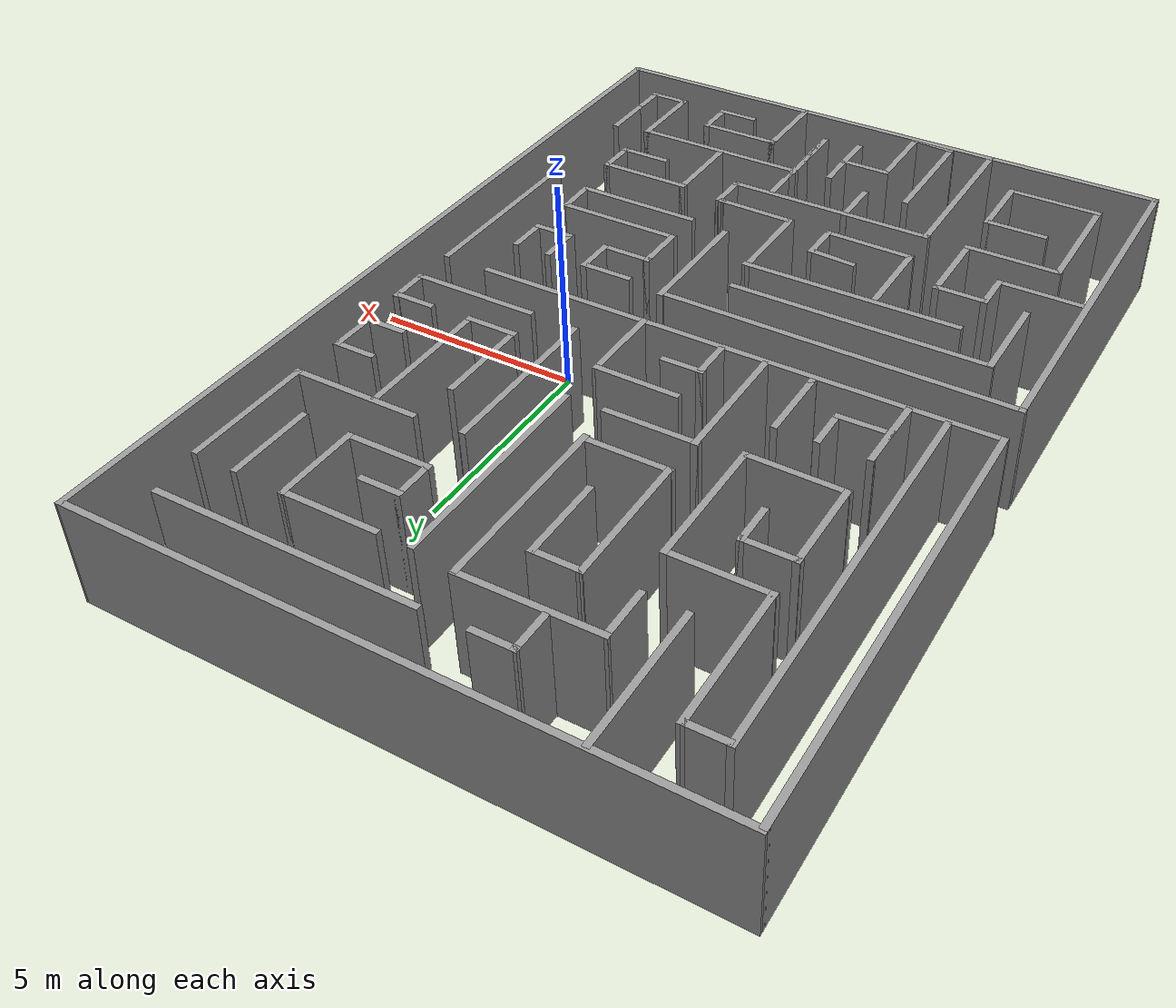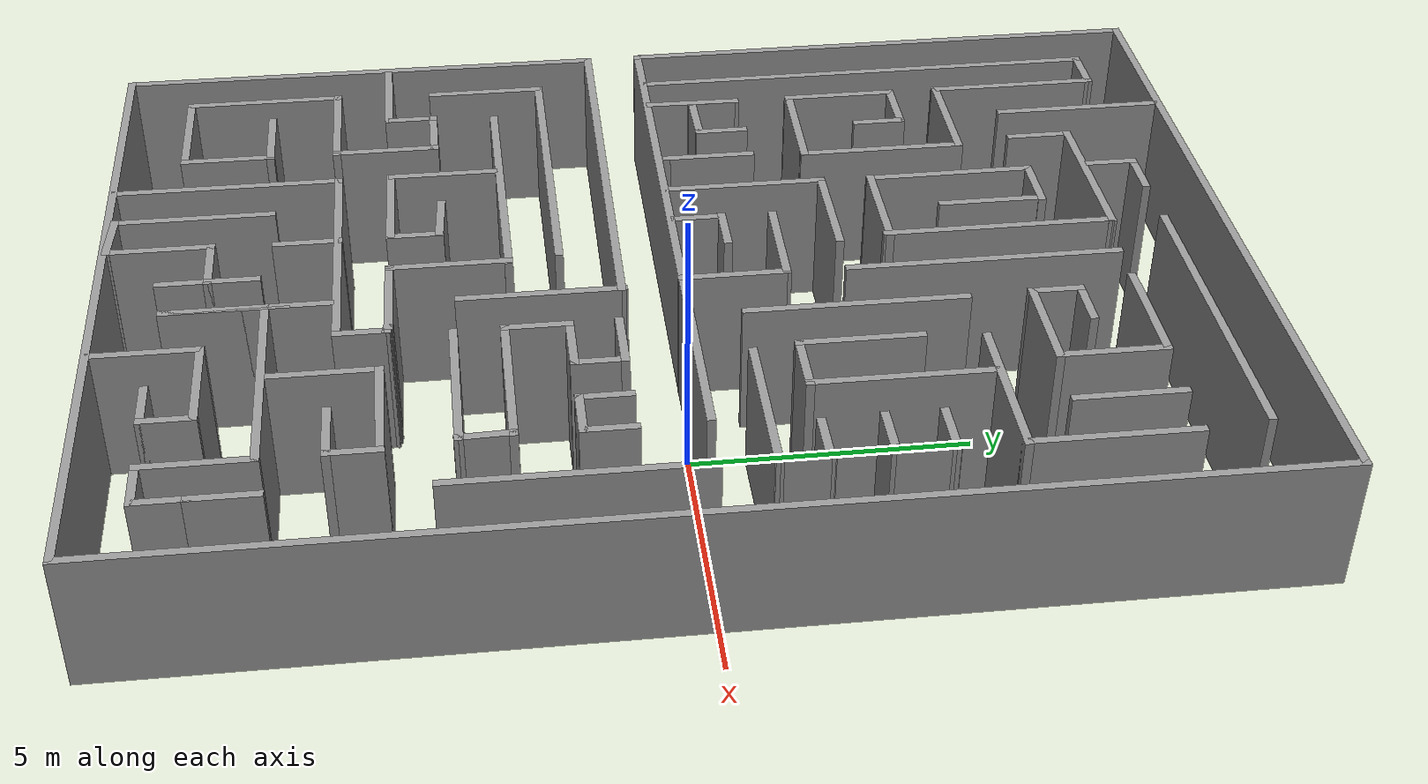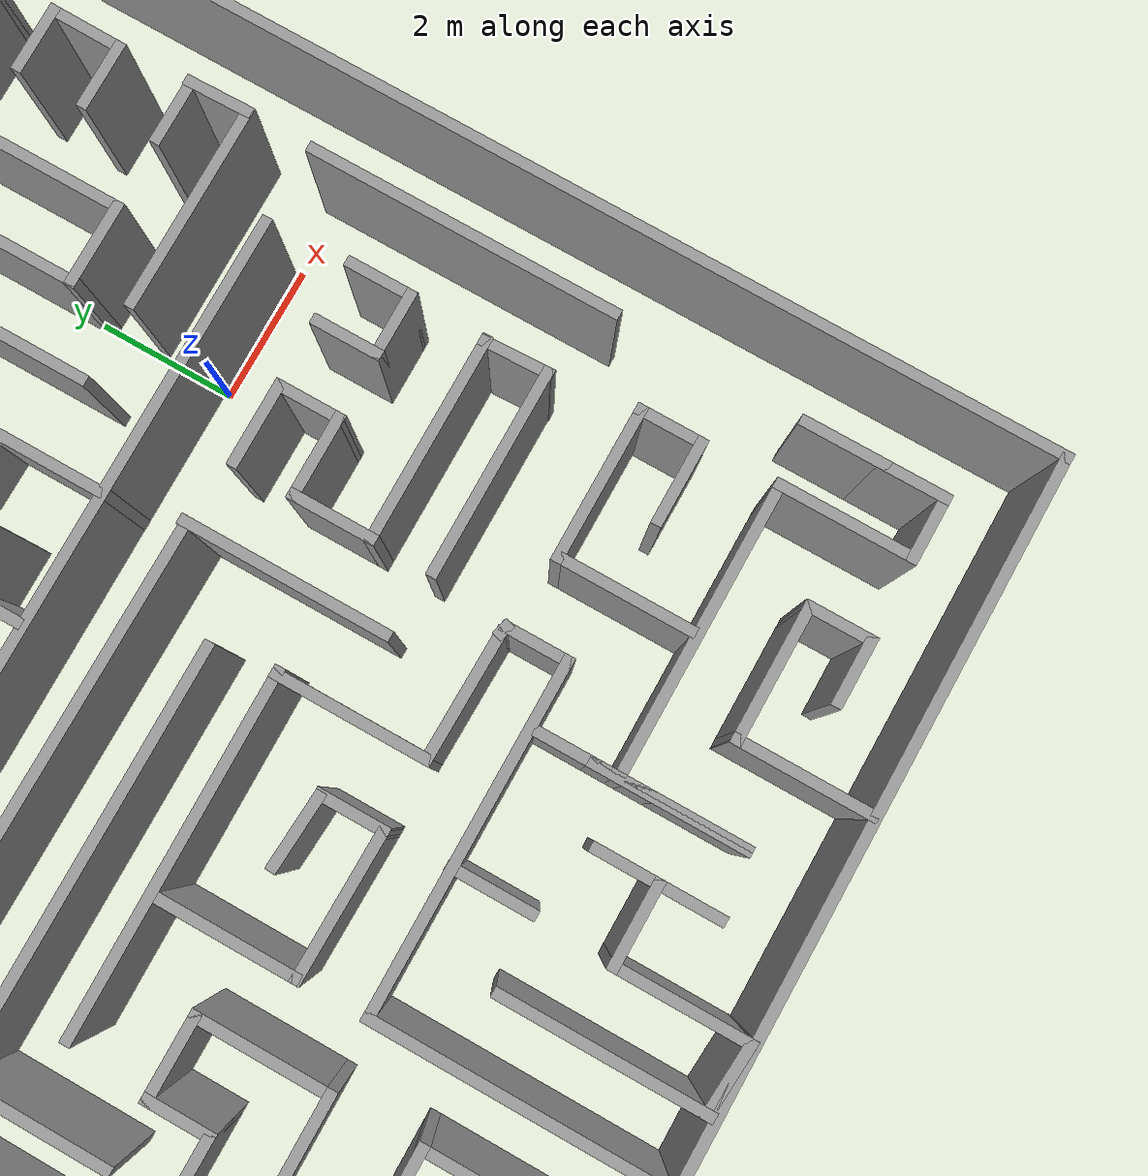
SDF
<sdf version='1.5'>
    <model name='Maze2'>
      <pose>-2.952 0.082564 0 0 -0 0</pose>
      <link name='Wall_0'>
        <collision name='Wall_0_Collision'>
          <geometry>
            <box>
              <size>3 0.15 2.5</size>
            </box>
          </geometry>
          <pose>0 0 1.25 0 -0 0</pose>
          <max_contacts>10</max_contacts>
          <surface>
            <contact>
              <ode/>
            </contact>
            <bounce/>
            <friction>
              <torsional>
                <ode/>
              </torsional>
              <ode/>
            </friction>
          </surface>
        </collision>
        <visual name='Wall_0_Visual'>
          <pose>0 0 1.25 0 -0 0</pose>
          <geometry>
            <box>
              <size>3 0.15 2.5</size>
            </box>
          </geometry>
          <material>
            <script>
              <uri>file://media/materials/scripts/gazebo.material</uri>
              <name>Gazebo/Grey</name>
            </script>
            <ambient>1 1 1 1</ambient>
          </material>
          <meta>
            <layer>0</layer>
          </meta>
        </visual>
        <pose>1.05662 -2.41881 0 0 -0 1.5708</pose>
        <self_collide>0</self_collide>
        <enable_wind>0</enable_wind>
        <kinematic>0</kinematic>
      </link>
      <link name='Wall_1'>
        <collision name='Wall_1_Collision'>
          <geometry>
            <box>
              <size>8.23971 0.15 2.5</size>
            </box>
          </geometry>
          <pose>0 0 1.25 0 -0 0</pose>
          <max_contacts>10</max_contacts>
          <surface>
            <contact>
              <ode/>
            </contact>
            <bounce/>
            <friction>
              <torsional>
                <ode/>
              </torsional>
              <ode/>
            </friction>
          </surface>
        </collision>
        <visual name='Wall_1_Visual'>
          <pose>0 0 1.25 0 -0 0</pose>
          <geometry>
            <box>
              <size>8.23971 0.15 2.5</size>
            </box>
          </geometry>
          <material>
            <script>
              <uri>file://media/materials/scripts/gazebo.material</uri>
              <name>Gazebo/Grey</name>
            </script>
            <ambient>1 1 1 1</ambient>
          </material>
          <meta>
            <layer>0</layer>
          </meta>
        </visual>
        <pose>-2.9881 -0.991516 0 0 -0 3.13346</pose>
        <self_collide>0</self_collide>
        <enable_wind>0</enable_wind>
        <kinematic>0</kinematic>
      </link>
      <link name='Wall_10'>
        <collision name='Wall_10_Collision'>
          <geometry>
            <box>
              <size>2.21006 0.15 2.5</size>
            </box>
          </geometry>
          <pose>0 0 1.25 0 -0 0</pose>
          <max_contacts>10</max_contacts>
          <surface>
            <contact>
              <ode/>
            </contact>
            <bounce/>
            <friction>
              <torsional>
                <ode/>
              </torsional>
              <ode/>
            </friction>
          </surface>
        </collision>
        <visual name='Wall_10_Visual'>
          <pose>0 0 1.25 0 -0 0</pose>
          <geometry>
            <box>
              <size>2.21006 0.15 2.5</size>
            </box>
          </geometry>
          <material>
            <script>
              <uri>file://media/materials/scripts/gazebo.material</uri>
              <name>Gazebo/Grey</name>
            </script>
            <ambient>1 1 1 1</ambient>
          </material>
          <meta>
            <layer>0</layer>
          </meta>
        </visual>
        <pose>-5.99208 -3.09041 0 0 -0 -1.57273</pose>
        <self_collide>0</self_collide>
        <enable_wind>0</enable_wind>
        <kinematic>0</kinematic>
      </link>
      <link name='Wall_100'>
        <collision name='Wall_100_Collision'>
          <geometry>
            <box>
              <size>1 0.15 2.5</size>
            </box>
          </geometry>
          <pose>0 0 1.25 0 -0 0</pose>
          <max_contacts>10</max_contacts>
          <surface>
            <contact>
              <ode/>
            </contact>
            <bounce/>
            <friction>
              <torsional>
                <ode/>
              </torsional>
              <ode/>
            </friction>
          </surface>
        </collision>
        <visual name='Wall_100_Visual'>
          <pose>0 0 1.25 0 -0 0</pose>
          <geometry>
            <box>
              <size>1 0.15 2.5</size>
            </box>
          </geometry>
          <material>
            <script>
              <uri>file://media/materials/scripts/gazebo.material</uri>
              <name>Gazebo/Grey</name>
            </script>
            <ambient>1 1 1 1</ambient>
          </material>
          <meta>
            <layer>0</layer>
          </meta>
        </visual>
        <pose>3.45154 -9.03895 0 0 -0 3.14159</pose>
        <self_collide>0</self_collide>
        <enable_wind>0</enable_wind>
        <kinematic>0</kinematic>
      </link>
      <link name='Wall_102'>
        <collision name='Wall_102_Collision'>
          <geometry>
            <box>
              <size>1 0.15 2.5</size>
            </box>
          </geometry>
          <pose>0 0 1.25 0 -0 0</pose>
          <max_contacts>10</max_contacts>
          <surface>
            <contact>
              <ode/>
            </contact>
            <bounce/>
            <friction>
              <torsional>
                <ode/>
              </torsional>
              <ode/>
            </friction>
          </surface>
        </collision>
        <visual name='Wall_102_Visual'>
          <pose>0 0 1.25 0 -0 0</pose>
          <geometry>
            <box>
              <size>1 0.15 2.5</size>
            </box>
          </geometry>
          <material>
            <script>
              <uri>file://media/materials/scripts/gazebo.material</uri>
              <name>Gazebo/Grey</name>
            </script>
            <ambient>1 1 1 1</ambient>
          </material>
          <meta>
            <layer>0</layer>
          </meta>
        </visual>
        <pose>0.053539 -8.60778 0 0 -0 -1.5708</pose>
        <self_collide>0</self_collide>
        <enable_wind>0</enable_wind>
        <kinematic>0</kinematic>
      </link>
      <link name='Wall_104'>
        <collision name='Wall_104_Collision'>
          <geometry>
            <box>
              <size>5 0.15 2.5</size>
            </box>
          </geometry>
          <pose>0 0 1.25 0 -0 0</pose>
          <max_contacts>10</max_contacts>
          <surface>
            <contact>
              <ode/>
            </contact>
            <bounce/>
            <friction>
              <torsional>
                <ode/>
              </torsional>
              <ode/>
            </friction>
          </surface>
        </collision>
        <visual name='Wall_104_Visual'>
          <pose>0 0 1.25 0 -0 0</pose>
          <geometry>
            <box>
              <size>5 0.15 2.5</size>
            </box>
          </geometry>
          <material>
            <script>
              <uri>file://media/materials/scripts/gazebo.material</uri>
              <name>Gazebo/Grey</name>
            </script>
            <ambient>1 1 1 1</ambient>
          </material>
          <meta>
            <layer>0</layer>
          </meta>
        </visual>
        <pose>0.885547 5.45052 0 0 -0 1.5708</pose>
        <self_collide>0</self_collide>
        <enable_wind>0</enable_wind>
        <kinematic>0</kinematic>
      </link>
      <link name='Wall_106'>
        <collision name='Wall_106_Collision'>
          <geometry>
            <box>
              <size>6 0.15 2.5</size>
            </box>
          </geometry>
          <pose>0 0 1.25 0 -0 0</pose>
          <max_contacts>10</max_contacts>
          <surface>
            <contact>
              <ode/>
            </contact>
            <bounce/>
            <friction>
              <torsional>
                <ode/>
              </torsional>
              <ode/>
            </friction>
          </surface>
        </collision>
        <visual name='Wall_106_Visual'>
          <pose>0 0 1.25 0 -0 0</pose>
          <geometry>
            <box>
              <size>6 0.15 2.5</size>
            </box>
          </geometry>
          <material>
            <script>
              <uri>file://media/materials/scripts/gazebo.material</uri>
              <name>Gazebo/Grey</name>
            </script>
            <ambient>1 1 1 1</ambient>
          </material>
          <meta>
            <layer>0</layer>
          </meta>
        </visual>
        <pose>2.87435 9.00269 0 0 -0 0</pose>
        <self_collide>0</self_collide>
        <enable_wind>0</enable_wind>
        <kinematic>0</kinematic>
      </link>
      <link name='Wall_108'>
        <collision name='Wall_108_Collision'>
          <geometry>
            <box>
              <size>2.25 0.15 2.5</size>
            </box>
          </geometry>
          <pose>0 0 1.25 0 -0 0</pose>
          <max_contacts>10</max_contacts>
          <surface>
            <contact>
              <ode/>
            </contact>
            <bounce/>
            <friction>
              <torsional>
                <ode/>
              </torsional>
              <ode/>
            </friction>
          </surface>
        </collision>
        <visual name='Wall_108_Visual'>
          <pose>0 0 1.25 0 -0 0</pose>
          <geometry>
            <box>
              <size>2.25 0.15 2.5</size>
            </box>
          </geometry>
          <material>
            <script>
              <uri>file://media/materials/scripts/gazebo.material</uri>
              <name>Gazebo/Grey</name>
            </script>
            <ambient>1 1 1 1</ambient>
          </material>
          <meta>
            <layer>0</layer>
          </meta>
        </visual>
        <pose>2.74179 7.89809 0 0 -0 0</pose>
        <self_collide>0</self_collide>
        <enable_wind>0</enable_wind>
        <kinematic>0</kinematic>
      </link>
      <link name='Wall_109'>
        <collision name='Wall_109_Collision'>
          <geometry>
            <box>
              <size>2 0.15 2.5</size>
            </box>
          </geometry>
          <pose>0 0 1.25 0 -0 0</pose>
          <max_contacts>10</max_contacts>
          <surface>
            <contact>
              <ode/>
            </contact>
            <bounce/>
            <friction>
              <torsional>
                <ode/>
              </torsional>
              <ode/>
            </friction>
          </surface>
        </collision>
        <visual name='Wall_109_Visual'>
          <pose>0 0 1.25 0 -0 0</pose>
          <geometry>
            <box>
              <size>2 0.15 2.5</size>
            </box>
          </geometry>
          <material>
            <script>
              <uri>file://media/materials/scripts/gazebo.material</uri>
              <name>Gazebo/Grey</name>
            </script>
            <ambient>1 1 1 1</ambient>
          </material>
          <meta>
            <layer>0</layer>
          </meta>
        </visual>
        <pose>3.79179 6.97309 0 0 -0 -1.5708</pose>
        <self_collide>0</self_collide>
        <enable_wind>0</enable_wind>
        <kinematic>0</kinematic>
      </link>
      <link name='Wall_110'>
        <collision name='Wall_110_Collision'>
          <geometry>
            <box>
              <size>2 0.15 2.5</size>
            </box>
          </geometry>
          <pose>0 0 1.25 0 -0 0</pose>
          <max_contacts>10</max_contacts>
          <surface>
            <contact>
              <ode/>
            </contact>
            <bounce/>
            <friction>
              <torsional>
                <ode/>
              </torsional>
              <ode/>
            </friction>
          </surface>
        </collision>
        <visual name='Wall_110_Visual'>
          <pose>0 0 1.25 0 -0 0</pose>
          <geometry>
            <box>
              <size>2 0.15 2.5</size>
            </box>
          </geometry>
          <material>
            <script>
              <uri>file://media/materials/scripts/gazebo.material</uri>
              <name>Gazebo/Grey</name>
            </script>
            <ambient>1 1 1 1</ambient>
          </material>
          <meta>
            <layer>0</layer>
          </meta>
        </visual>
        <pose>2.86679 6.04809 0 0 -0 3.14159</pose>
        <self_collide>0</self_collide>
        <enable_wind>0</enable_wind>
        <kinematic>0</kinematic>
      </link>
      <link name='Wall_111'>
        <collision name='Wall_111_Collision'>
          <geometry>
            <box>
              <size>1 0.15 2.5</size>
            </box>
          </geometry>
          <pose>0 0 1.25 0 -0 0</pose>
          <max_contacts>10</max_contacts>
          <surface>
            <contact>
              <ode/>
            </contact>
            <bounce/>
            <friction>
              <torsional>
                <ode/>
              </torsional>
              <ode/>
            </friction>
          </surface>
        </collision>
        <visual name='Wall_111_Visual'>
          <pose>0 0 1.25 0 -0 0</pose>
          <geometry>
            <box>
              <size>1 0.15 2.5</size>
            </box>
          </geometry>
          <material>
            <script>
              <uri>file://media/materials/scripts/gazebo.material</uri>
              <name>Gazebo/Grey</name>
            </script>
            <ambient>1 1 1 1</ambient>
          </material>
          <meta>
            <layer>0</layer>
          </meta>
        </visual>
        <pose>1.94179 6.47309 0 0 -0 1.5708</pose>
        <self_collide>0</self_collide>
        <enable_wind>0</enable_wind>
        <kinematic>0</kinematic>
      </link>
      <link name='Wall_112'>
        <collision name='Wall_112_Collision'>
          <geometry>
            <box>
              <size>1 0.15 2.5</size>
            </box>
          </geometry>
          <pose>0 0 1.25 0 -0 0</pose>
          <max_contacts>10</max_contacts>
          <surface>
            <contact>
              <ode/>
            </contact>
            <bounce/>
            <friction>
              <torsional>
                <ode/>
              </torsional>
              <ode/>
            </friction>
          </surface>
        </collision>
        <visual name='Wall_112_Visual'>
          <pose>0 0 1.25 0 -0 0</pose>
          <geometry>
            <box>
              <size>1 0.15 2.5</size>
            </box>
          </geometry>
          <material>
            <script>
              <uri>file://media/materials/scripts/gazebo.material</uri>
              <name>Gazebo/Grey</name>
            </script>
            <ambient>1 1 1 1</ambient>
          </material>
          <meta>
            <layer>0</layer>
          </meta>
        </visual>
        <pose>2.36679 6.89809 0 0 -0 0</pose>
        <self_collide>0</self_collide>
        <enable_wind>0</enable_wind>
        <kinematic>0</kinematic>
      </link>
      <link name='Wall_114'>
        <collision name='Wall_114_Collision'>
          <geometry>
            <box>
              <size>4 0.15 2.5</size>
            </box>
          </geometry>
          <pose>0 0 1.25 0 -0 0</pose>
          <max_contacts>10</max_contacts>
          <surface>
            <contact>
              <ode/>
            </contact>
            <bounce/>
            <friction>
              <torsional>
                <ode/>
              </torsional>
              <ode/>
            </friction>
          </surface>
        </collision>
        <visual name='Wall_114_Visual'>
          <pose>0 0 1.25 0 -0 0</pose>
          <geometry>
            <box>
              <size>4 0.15 2.5</size>
            </box>
          </geometry>
          <material>
            <script>
              <uri>file://media/materials/scripts/gazebo.material</uri>
              <name>Gazebo/Grey</name>
            </script>
            <ambient>1 1 1 1</ambient>
          </material>
          <meta>
            <layer>0</layer>
          </meta>
        </visual>
        <pose>1.96588 2.95915 0 0 -0 -1.5708</pose>
        <self_collide>0</self_collide>
        <enable_wind>0</enable_wind>
        <kinematic>0</kinematic>
      </link>
      <link name='Wall_116'>
        <collision name='Wall_116_Collision'>
          <geometry>
            <box>
              <size>3 0.15 2.5</size>
            </box>
          </geometry>
          <pose>0 0 1.25 0 -0 0</pose>
          <max_contacts>10</max_contacts>
          <surface>
            <contact>
              <ode/>
            </contact>
            <bounce/>
            <friction>
              <torsional>
                <ode/>
              </torsional>
              <ode/>
            </friction>
          </surface>
        </collision>
        <visual name='Wall_116_Visual'>
          <pose>0 0 1.25 0 -0 0</pose>
          <geometry>
            <box>
              <size>3 0.15 2.5</size>
            </box>
          </geometry>
          <material>
            <script>
              <uri>file://media/materials/scripts/gazebo.material</uri>
              <name>Gazebo/Grey</name>
            </script>
            <ambient>1 1 1 1</ambient>
          </material>
          <meta>
            <layer>0</layer>
          </meta>
        </visual>
        <pose>4.55311 4.97074 0 0 -0 0</pose>
        <self_collide>0</self_collide>
        <enable_wind>0</enable_wind>
        <kinematic>0</kinematic>
      </link>
      <link name='Wall_118'>
        <collision name='Wall_118_Collision'>
          <geometry>
            <box>
              <size>2 0.15 2.5</size>
            </box>
          </geometry>
          <pose>0 0 1.25 0 -0 0</pose>
          <max_contacts>10</max_contacts>
          <surface>
            <contact>
              <ode/>
            </contact>
            <bounce/>
            <friction>
              <torsional>
                <ode/>
              </torsional>
              <ode/>
            </friction>
          </surface>
        </collision>
        <visual name='Wall_118_Visual'>
          <pose>0 0 1.25 0 -0 0</pose>
          <geometry>
            <box>
              <size>2 0.15 2.5</size>
            </box>
          </geometry>
          <material>
            <script>
              <uri>file://media/materials/scripts/gazebo.material</uri>
              <name>Gazebo/Grey</name>
            </script>
            <ambient>1 1 1 1</ambient>
          </material>
          <meta>
            <layer>0</layer>
          </meta>
        </visual>
        <pose>4.96128 6.9316 0 0 -0 1.5708</pose>
        <self_collide>0</self_collide>
        <enable_wind>0</enable_wind>
        <kinematic>0</kinematic>
      </link>
      <link name='Wall_12'>
        <collision name='Wall_12_Collision'>
          <geometry>
            <box>
              <size>5.1119 0.15 2.5</size>
            </box>
          </geometry>
          <pose>0 0 1.25 0 -0 0</pose>
          <max_contacts>10</max_contacts>
          <surface>
            <contact>
              <ode/>
            </contact>
            <bounce/>
            <friction>
              <torsional>
                <ode/>
              </torsional>
              <ode/>
            </friction>
          </surface>
        </collision>
        <visual name='Wall_12_Visual'>
          <pose>0 0 1.25 0 -0 0</pose>
          <geometry>
            <box>
              <size>5.1119 0.15 2.5</size>
            </box>
          </geometry>
          <material>
            <script>
              <uri>file://media/materials/scripts/gazebo.material</uri>
              <name>Gazebo/Grey</name>
            </script>
            <ambient>1 1 1 1</ambient>
          </material>
          <meta>
            <layer>0</layer>
          </meta>
        </visual>
        <pose>-2.46512 -2.94659 0 0 -0 0.006165</pose>
        <self_collide>0</self_collide>
        <enable_wind>0</enable_wind>
        <kinematic>0</kinematic>
      </link>
      <link name='Wall_120'>
        <collision name='Wall_120_Collision'>
          <geometry>
            <box>
              <size>3 0.15 2.5</size>
            </box>
          </geometry>
          <pose>0 0 1.25 0 -0 0</pose>
          <max_contacts>10</max_contacts>
          <surface>
            <contact>
              <ode/>
            </contact>
            <bounce/>
            <friction>
              <torsional>
                <ode/>
              </torsional>
              <ode/>
            </friction>
          </surface>
        </collision>
        <visual name='Wall_120_Visual'>
          <pose>0 0 1.25 0 -0 0</pose>
          <geometry>
            <box>
              <size>3 0.15 2.5</size>
            </box>
          </geometry>
          <material>
            <script>
              <uri>file://media/materials/scripts/gazebo.material</uri>
              <name>Gazebo/Grey</name>
            </script>
            <ambient>1 1 1 1</ambient>
          </material>
          <meta>
            <layer>0</layer>
          </meta>
        </visual>
        <pose>5.96654 6.39574 0 0 -0 1.5708</pose>
        <self_collide>0</self_collide>
        <enable_wind>0</enable_wind>
        <kinematic>0</kinematic>
      </link>
      <link name='Wall_122'>
        <collision name='Wall_122_Collision'>
          <geometry>
            <box>
              <size>3.25 0.15 2.5</size>
            </box>
          </geometry>
          <pose>0 0 1.25 0 -0 0</pose>
          <max_contacts>10</max_contacts>
          <surface>
            <contact>
              <ode/>
            </contact>
            <bounce/>
            <friction>
              <torsional>
                <ode/>
              </torsional>
              <ode/>
            </friction>
          </surface>
        </collision>
        <visual name='Wall_122_Visual'>
          <pose>0 0 1.25 0 -0 0</pose>
          <geometry>
            <box>
              <size>3.25 0.15 2.5</size>
            </box>
          </geometry>
          <material>
            <script>
              <uri>file://media/materials/scripts/gazebo.material</uri>
              <name>Gazebo/Grey</name>
            </script>
            <ambient>1 1 1 1</ambient>
          </material>
          <meta>
            <layer>0</layer>
          </meta>
        </visual>
        <pose>4.07457 3.33741 0 0 -0 -1.5708</pose>
        <self_collide>0</self_collide>
        <enable_wind>0</enable_wind>
        <kinematic>0</kinematic>
      </link>
      <link name='Wall_123'>
        <collision name='Wall_123_Collision'>
          <geometry>
            <box>
              <size>1.25 0.15 2.5</size>
            </box>
          </geometry>
          <pose>0 0 1.25 0 -0 0</pose>
          <max_contacts>10</max_contacts>
          <surface>
            <contact>
              <ode/>
            </contact>
            <bounce/>
            <friction>
              <torsional>
                <ode/>
              </torsional>
              <ode/>
            </friction>
          </surface>
        </collision>
        <visual name='Wall_123_Visual'>
          <pose>0 0 1.25 0 -0 0</pose>
          <geometry>
            <box>
              <size>1.25 0.15 2.5</size>
            </box>
          </geometry>
          <material>
            <script>
              <uri>file://media/materials/scripts/gazebo.material</uri>
              <name>Gazebo/Grey</name>
            </script>
            <ambient>1 1 1 1</ambient>
          </material>
          <meta>
            <layer>0</layer>
          </meta>
        </visual>
        <pose>3.52457 1.78741 0 0 -0 3.14159</pose>
        <self_collide>0</self_collide>
        <enable_wind>0</enable_wind>
        <kinematic>0</kinematic>
      </link>
      <link name='Wall_124'>
        <collision name='Wall_124_Collision'>
          <geometry>
            <box>
              <size>2.25 0.15 2.5</size>
            </box>
          </geometry>
          <pose>0 0 1.25 0 -0 0</pose>
          <max_contacts>10</max_contacts>
          <surface>
            <contact>
              <ode/>
            </contact>
            <bounce/>
            <friction>
              <torsional>
                <ode/>
              </torsional>
              <ode/>
            </friction>
          </surface>
        </collision>
        <visual name='Wall_124_Visual'>
          <pose>0 0 1.25 0 -0 0</pose>
          <geometry>
            <box>
              <size>2.25 0.15 2.5</size>
            </box>
          </geometry>
          <material>
            <script>
              <uri>file://media/materials/scripts/gazebo.material</uri>
              <name>Gazebo/Grey</name>
            </script>
            <ambient>1 1 1 1</ambient>
          </material>
          <meta>
            <layer>0</layer>
          </meta>
        </visual>
        <pose>2.97457 2.83741 0 0 -0 1.5708</pose>
        <self_collide>0</self_collide>
        <enable_wind>0</enable_wind>
        <kinematic>0</kinematic>
      </link>
      <link name='Wall_126'>
        <collision name='Wall_126_Collision'>
          <geometry>
            <box>
              <size>1 0.15 2.5</size>
            </box>
          </geometry>
          <pose>0 0 1.25 0 -0 0</pose>
          <max_contacts>10</max_contacts>
          <surface>
            <contact>
              <ode/>
            </contact>
            <bounce/>
            <friction>
              <torsional>
                <ode/>
              </torsional>
              <ode/>
            </friction>
          </surface>
        </collision>
        <visual name='Wall_126_Visual'>
          <pose>0 0 1.25 0 -0 0</pose>
          <geometry>
            <box>
              <size>1 0.15 2.5</size>
            </box>
          </geometry>
          <material>
            <script>
              <uri>file://media/materials/scripts/gazebo.material</uri>
              <name>Gazebo/Grey</name>
            </script>
            <ambient>1 1 1 1</ambient>
          </material>
          <meta>
            <layer>0</layer>
          </meta>
        </visual>
        <pose>5.47761 3.83472 0 0 -0 0</pose>
        <self_collide>0</self_collide>
        <enable_wind>0</enable_wind>
        <kinematic>0</kinematic>
      </link>
      <link name='Wall_127'>
        <collision name='Wall_127_Collision'>
          <geometry>
            <box>
              <size>1.11415 0.15 2.5</size>
            </box>
          </geometry>
          <pose>0 0 1.25 0 -0 0</pose>
          <max_contacts>10</max_contacts>
          <surface>
            <contact>
              <ode/>
            </contact>
            <bounce/>
            <friction>
              <torsional>
                <ode/>
              </torsional>
              <ode/>
            </friction>
          </surface>
        </collision>
        <visual name='Wall_127_Visual'>
          <pose>0 0 1.25 0 -0 0</pose>
          <geometry>
            <box>
              <size>1.11415 0.15 2.5</size>
            </box>
          </geometry>
          <material>
            <script>
              <uri>file://media/materials/scripts/gazebo.material</uri>
              <name>Gazebo/Grey</name>
            </script>
            <ambient>1 1 1 1</ambient>
          </material>
          <meta>
            <layer>0</layer>
          </meta>
        </visual>
        <pose>5.89623 3.34508 0 0 -0 -1.58403</pose>
        <self_collide>0</self_collide>
        <enable_wind>0</enable_wind>
        <kinematic>0</kinematic>
      </link>
      <link name='Wall_128'>
        <collision name='Wall_128_Collision'>
          <geometry>
            <box>
              <size>1 0.15 2.5</size>
            </box>
          </geometry>
          <pose>0 0 1.25 0 -0 0</pose>
          <max_contacts>10</max_contacts>
          <surface>
            <contact>
              <ode/>
            </contact>
            <bounce/>
            <friction>
              <torsional>
                <ode/>
              </torsional>
              <ode/>
            </friction>
          </surface>
        </collision>
        <visual name='Wall_128_Visual'>
          <pose>0 0 1.25 0 -0 0</pose>
          <geometry>
            <box>
              <size>1 0.15 2.5</size>
            </box>
          </geometry>
          <material>
            <script>
              <uri>file://media/materials/scripts/gazebo.material</uri>
              <name>Gazebo/Grey</name>
            </script>
            <ambient>1 1 1 1</ambient>
          </material>
          <meta>
            <layer>0</layer>
          </meta>
        </visual>
        <pose>5.46485 2.85545 0 0 -0 3.14159</pose>
        <self_collide>0</self_collide>
        <enable_wind>0</enable_wind>
        <kinematic>0</kinematic>
      </link>
      <link name='Wall_13'>
        <collision name='Wall_13_Collision'>
          <geometry>
            <box>
              <size>2.25 0.15 2.5</size>
            </box>
          </geometry>
          <pose>0 0 1.25 0 -0 0</pose>
          <max_contacts>10</max_contacts>
          <surface>
            <contact>
              <ode/>
            </contact>
            <bounce/>
            <friction>
              <torsional>
                <ode/>
              </torsional>
              <ode/>
            </friction>
          </surface>
        </collision>
        <visual name='Wall_13_Visual'>
          <pose>0 0 1.25 0 -0 0</pose>
          <geometry>
            <box>
              <size>2.25 0.15 2.5</size>
            </box>
          </geometry>
          <material>
            <script>
              <uri>file://media/materials/scripts/gazebo.material</uri>
              <name>Gazebo/Grey</name>
            </script>
            <ambient>1 1 1 1</ambient>
          </material>
          <meta>
            <layer>0</layer>
          </meta>
        </visual>
        <pose>-0.014812 -3.9813 0 0 -0 -1.5708</pose>
        <self_collide>0</self_collide>
        <enable_wind>0</enable_wind>
        <kinematic>0</kinematic>
      </link>
      <link name='Wall_130'>
        <collision name='Wall_130_Collision'>
          <geometry>
            <box>
              <size>3 0.15 2.5</size>
            </box>
          </geometry>
          <pose>0 0 1.25 0 -0 0</pose>
          <max_contacts>10</max_contacts>
          <surface>
            <contact>
              <ode/>
            </contact>
            <bounce/>
            <friction>
              <torsional>
                <ode/>
              </torsional>
              <ode/>
            </friction>
          </surface>
        </collision>
        <visual name='Wall_130_Visual'>
          <pose>0 0 1.25 0 -0 0</pose>
          <geometry>
            <box>
              <size>3 0.15 2.5</size>
            </box>
          </geometry>
          <material>
            <script>
              <uri>file://media/materials/scripts/gazebo.material</uri>
              <name>Gazebo/Grey</name>
            </script>
            <ambient>1 1 1 1</ambient>
          </material>
          <meta>
            <layer>0</layer>
          </meta>
        </visual>
        <pose>4.52953 0.989447 0 0 -0 0</pose>
        <self_collide>0</self_collide>
        <enable_wind>0</enable_wind>
        <kinematic>0</kinematic>
      </link>
      <link name='Wall_131'>
        <collision name='Wall_131_Collision'>
          <geometry>
            <box>
              <size>0.969553 0.15 2.5</size>
            </box>
          </geometry>
          <pose>0 0 1.25 0 -0 0</pose>
          <max_contacts>10</max_contacts>
          <surface>
            <contact>
              <ode/>
            </contact>
            <bounce/>
            <friction>
              <torsional>
                <ode/>
              </torsional>
              <ode/>
            </friction>
          </surface>
        </collision>
        <visual name='Wall_131_Visual'>
          <pose>0 0 1.25 0 -0 0</pose>
          <geometry>
            <box>
              <size>0.969553 0.15 2.5</size>
            </box>
          </geometry>
          <material>
            <script>
              <uri>file://media/materials/scripts/gazebo.material</uri>
              <name>Gazebo/Grey</name>
            </script>
            <ambient>1 1 1 1</ambient>
          </material>
          <meta>
            <layer>0</layer>
          </meta>
        </visual>
        <pose>5.94688 1.41445 0 0 -0 1.58946</pose>
        <self_collide>0</self_collide>
        <enable_wind>0</enable_wind>
        <kinematic>0</kinematic>
      </link>
      <link name='Wall_132'>
        <collision name='Wall_132_Collision'>
          <geometry>
            <box>
              <size>1 0.15 2.5</size>
            </box>
          </geometry>
          <pose>0 0 1.25 0 -0 0</pose>
          <max_contacts>10</max_contacts>
          <surface>
            <contact>
              <ode/>
            </contact>
            <bounce/>
            <friction>
              <torsional>
                <ode/>
              </torsional>
              <ode/>
            </friction>
          </surface>
        </collision>
        <visual name='Wall_132_Visual'>
          <pose>0 0 1.25 0 -0 0</pose>
          <geometry>
            <box>
              <size>1 0.15 2.5</size>
            </box>
          </geometry>
          <material>
            <script>
              <uri>file://media/materials/scripts/gazebo.material</uri>
              <name>Gazebo/Grey</name>
            </script>
            <ambient>1 1 1 1</ambient>
          </material>
          <meta>
            <layer>0</layer>
          </meta>
        </visual>
        <pose>5.51424 1.80886 0 0 -0 3.14159</pose>
        <self_collide>0</self_collide>
        <enable_wind>0</enable_wind>
        <kinematic>0</kinematic>
      </link>
      <link name='Wall_134'>
        <collision name='Wall_134_Collision'>
          <geometry>
            <box>
              <size>4.5 0.15 2.5</size>
            </box>
          </geometry>
          <pose>0 0 1.25 0 -0 0</pose>
          <max_contacts>10</max_contacts>
          <surface>
            <contact>
              <ode/>
            </contact>
            <bounce/>
            <friction>
              <torsional>
                <ode/>
              </torsional>
              <ode/>
            </friction>
          </surface>
        </collision>
        <visual name='Wall_134_Visual'>
          <pose>0 0 1.25 0 -0 0</pose>
          <geometry>
            <box>
              <size>4.5 0.15 2.5</size>
            </box>
          </geometry>
          <material>
            <script>
              <uri>file://media/materials/scripts/gazebo.material</uri>
              <name>Gazebo/Grey</name>
            </script>
            <ambient>1 1 1 1</ambient>
          </material>
          <meta>
            <layer>0</layer>
          </meta>
        </visual>
        <pose>5.9379 -2.1578 0 0 -0 -1.5708</pose>
        <self_collide>0</self_collide>
        <enable_wind>0</enable_wind>
        <kinematic>0</kinematic>
      </link>
      <link name='Wall_136'>
        <collision name='Wall_136_Collision'>
          <geometry>
            <box>
              <size>1 0.15 2.5</size>
            </box>
          </geometry>
          <pose>0 0 1.25 0 -0 0</pose>
          <max_contacts>10</max_contacts>
          <surface>
            <contact>
              <ode/>
            </contact>
            <bounce/>
            <friction>
              <torsional>
                <ode/>
              </torsional>
              <ode/>
            </friction>
          </surface>
        </collision>
        <visual name='Wall_136_Visual'>
          <pose>0 0 1.25 0 -0 0</pose>
          <geometry>
            <box>
              <size>1 0.15 2.5</size>
            </box>
          </geometry>
          <material>
            <script>
              <uri>file://media/materials/scripts/gazebo.material</uri>
              <name>Gazebo/Grey</name>
            </script>
            <ambient>1 1 1 1</ambient>
          </material>
          <meta>
            <layer>0</layer>
          </meta>
        </visual>
        <pose>5.45373 -9.01313 0 0 -0 0</pose>
        <self_collide>0</self_collide>
        <enable_wind>0</enable_wind>
        <kinematic>0</kinematic>
      </link>
      <link name='Wall_137'>
        <collision name='Wall_137_Collision'>
          <geometry>
            <box>
              <size>1 0.15 2.5</size>
            </box>
          </geometry>
          <pose>0 0 1.25 0 -0 0</pose>
          <max_contacts>10</max_contacts>
          <surface>
            <contact>
              <ode/>
            </contact>
            <bounce/>
            <friction>
              <torsional>
                <ode/>
              </torsional>
              <ode/>
            </friction>
          </surface>
        </collision>
        <visual name='Wall_137_Visual'>
          <pose>0 0 1.25 0 -0 0</pose>
          <geometry>
            <box>
              <size>1 0.15 2.5</size>
            </box>
          </geometry>
          <material>
            <script>
              <uri>file://media/materials/scripts/gazebo.material</uri>
              <name>Gazebo/Grey</name>
            </script>
            <ambient>1 1 1 1</ambient>
          </material>
          <meta>
            <layer>0</layer>
          </meta>
        </visual>
        <pose>5.87873 -8.58813 0 0 -0 1.5708</pose>
        <self_collide>0</self_collide>
        <enable_wind>0</enable_wind>
        <kinematic>0</kinematic>
      </link>
      <link name='Wall_138'>
        <collision name='Wall_138_Collision'>
          <geometry>
            <box>
              <size>1.25 0.15 2.5</size>
            </box>
          </geometry>
          <pose>0 0 1.25 0 -0 0</pose>
          <max_contacts>10</max_contacts>
          <surface>
            <contact>
              <ode/>
            </contact>
            <bounce/>
            <friction>
              <torsional>
                <ode/>
              </torsional>
              <ode/>
            </friction>
          </surface>
        </collision>
        <visual name='Wall_138_Visual'>
          <pose>0 0 1.25 0 -0 0</pose>
          <geometry>
            <box>
              <size>1.25 0.15 2.5</size>
            </box>
          </geometry>
          <material>
            <script>
              <uri>file://media/materials/scripts/gazebo.material</uri>
              <name>Gazebo/Grey</name>
            </script>
            <ambient>1 1 1 1</ambient>
          </material>
          <meta>
            <layer>0</layer>
          </meta>
        </visual>
        <pose>5.87873 -7.61313 0 0 -0 1.5708</pose>
        <self_collide>0</self_collide>
        <enable_wind>0</enable_wind>
        <kinematic>0</kinematic>
      </link>
      <link name='Wall_14'>
        <collision name='Wall_14_Collision'>
          <geometry>
            <box>
              <size>1.88847 0.15 2.5</size>
            </box>
          </geometry>
          <pose>0 0 1.25 0 -0 0</pose>
          <max_contacts>10</max_contacts>
          <surface>
            <contact>
              <ode/>
            </contact>
            <bounce/>
            <friction>
              <torsional>
                <ode/>
              </torsional>
              <ode/>
            </friction>
          </surface>
        </collision>
        <visual name='Wall_14_Visual'>
          <pose>0 0 1.25 0 -0 0</pose>
          <geometry>
            <box>
              <size>1.88847 0.15 2.5</size>
            </box>
          </geometry>
          <material>
            <script>
              <uri>file://media/materials/scripts/gazebo.material</uri>
              <name>Gazebo/Grey</name>
            </script>
            <ambient>1 1 1 1</ambient>
          </material>
          <meta>
            <layer>0</layer>
          </meta>
        </visual>
        <pose>0.884876 -5.04659 0 0 -0 -0.017597</pose>
        <self_collide>0</self_collide>
        <enable_wind>0</enable_wind>
        <kinematic>0</kinematic>
      </link>
      <link name='Wall_140'>
        <collision name='Wall_140_Collision'>
          <geometry>
            <box>
              <size>2 0.15 2.5</size>
            </box>
          </geometry>
          <pose>0 0 1.25 0 -0 0</pose>
          <max_contacts>10</max_contacts>
          <surface>
            <contact>
              <ode/>
            </contact>
            <bounce/>
            <friction>
              <torsional>
                <ode/>
              </torsional>
              <ode/>
            </friction>
          </surface>
        </collision>
        <visual name='Wall_140_Visual'>
          <pose>0 0 1.25 0 -0 0</pose>
          <geometry>
            <box>
              <size>2 0.15 2.5</size>
            </box>
          </geometry>
          <material>
            <script>
              <uri>file://media/materials/scripts/gazebo.material</uri>
              <name>Gazebo/Grey</name>
            </script>
            <ambient>1 1 1 1</ambient>
          </material>
          <meta>
            <layer>0</layer>
          </meta>
        </visual>
        <pose>2.91262 -6.14071 0 0 -0 1.5708</pose>
        <self_collide>0</self_collide>
        <enable_wind>0</enable_wind>
        <kinematic>0</kinematic>
      </link>
      <link name='Wall_141'>
        <collision name='Wall_141_Collision'>
          <geometry>
            <box>
              <size>2.25 0.15 2.5</size>
            </box>
          </geometry>
          <pose>0 0 1.25 0 -0 0</pose>
          <max_contacts>10</max_contacts>
          <surface>
            <contact>
              <ode/>
            </contact>
            <bounce/>
            <friction>
              <torsional>
                <ode/>
              </torsional>
              <ode/>
            </friction>
          </surface>
        </collision>
        <visual name='Wall_141_Visual'>
          <pose>0 0 1.25 0 -0 0</pose>
          <geometry>
            <box>
              <size>2.25 0.15 2.5</size>
            </box>
          </geometry>
          <material>
            <script>
              <uri>file://media/materials/scripts/gazebo.material</uri>
              <name>Gazebo/Grey</name>
            </script>
            <ambient>1 1 1 1</ambient>
          </material>
          <meta>
            <layer>0</layer>
          </meta>
        </visual>
        <pose>3.96261 -5.21571 0 0 -0 0</pose>
        <self_collide>0</self_collide>
        <enable_wind>0</enable_wind>
        <kinematic>0</kinematic>
      </link>
      <link name='Wall_142'>
        <collision name='Wall_142_Collision'>
          <geometry>
            <box>
              <size>1 0.15 2.5</size>
            </box>
          </geometry>
          <pose>0 0 1.25 0 -0 0</pose>
          <max_contacts>10</max_contacts>
          <surface>
            <contact>
              <ode/>
            </contact>
            <bounce/>
            <friction>
              <torsional>
                <ode/>
              </torsional>
              <ode/>
            </friction>
          </surface>
        </collision>
        <visual name='Wall_142_Visual'>
          <pose>0 0 1.25 0 -0 0</pose>
          <geometry>
            <box>
              <size>1 0.15 2.5</size>
            </box>
          </geometry>
          <material>
            <script>
              <uri>file://media/materials/scripts/gazebo.material</uri>
              <name>Gazebo/Grey</name>
            </script>
            <ambient>1 1 1 1</ambient>
          </material>
          <meta>
            <layer>0</layer>
          </meta>
        </visual>
        <pose>5.01262 -5.64071 0 0 -0 -1.5708</pose>
        <self_collide>0</self_collide>
        <enable_wind>0</enable_wind>
        <kinematic>0</kinematic>
      </link>
      <link name='Wall_143'>
        <collision name='Wall_143_Collision'>
          <geometry>
            <box>
              <size>1.25 0.15 2.5</size>
            </box>
          </geometry>
          <pose>0 0 1.25 0 -0 0</pose>
          <max_contacts>10</max_contacts>
          <surface>
            <contact>
              <ode/>
            </contact>
            <bounce/>
            <friction>
              <torsional>
                <ode/>
              </torsional>
              <ode/>
            </friction>
          </surface>
        </collision>
        <visual name='Wall_143_Visual'>
          <pose>0 0 1.25 0 -0 0</pose>
          <geometry>
            <box>
              <size>1.25 0.15 2.5</size>
            </box>
          </geometry>
          <material>
            <script>
              <uri>file://media/materials/scripts/gazebo.material</uri>
              <name>Gazebo/Grey</name>
            </script>
            <ambient>1 1 1 1</ambient>
          </material>
          <meta>
            <layer>0</layer>
          </meta>
        </visual>
        <pose>4.46262 -6.06571 0 0 -0 3.14159</pose>
        <self_collide>0</self_collide>
        <enable_wind>0</enable_wind>
        <kinematic>0</kinematic>
      </link>
      <link name='Wall_145'>
        <collision name='Wall_145_Collision'>
          <geometry>
            <box>
              <size>3 0.15 2.5</size>
            </box>
          </geometry>
          <pose>0 0 1.25 0 -0 0</pose>
          <max_contacts>10</max_contacts>
          <surface>
            <contact>
              <ode/>
            </contact>
            <bounce/>
            <friction>
              <torsional>
                <ode/>
              </torsional>
              <ode/>
            </friction>
          </surface>
        </collision>
        <visual name='Wall_145_Visual'>
          <pose>0 0 1.25 0 -0 0</pose>
          <geometry>
            <box>
              <size>3 0.15 2.5</size>
            </box>
          </geometry>
          <material>
            <script>
              <uri>file://media/materials/scripts/gazebo.material</uri>
              <name>Gazebo/Grey</name>
            </script>
            <ambient>1 1 1 1</ambient>
          </material>
          <meta>
            <layer>0</layer>
          </meta>
        </visual>
        <pose>3.43258 -3.97421 0 0 -0 0</pose>
        <self_collide>0</self_collide>
        <enable_wind>0</enable_wind>
        <kinematic>0</kinematic>
      </link>
      <link name='Wall_146'>
        <collision name='Wall_146_Collision'>
          <geometry>
            <box>
              <size>1.03086 0.15 2.5</size>
            </box>
          </geometry>
          <pose>0 0 1.25 0 -0 0</pose>
          <max_contacts>10</max_contacts>
          <surface>
            <contact>
              <ode/>
            </contact>
            <bounce/>
            <friction>
              <torsional>
                <ode/>
              </torsional>
              <ode/>
            </friction>
          </surface>
        </collision>
        <visual name='Wall_146_Visual'>
          <pose>0 0 1.25 0 -0 0</pose>
          <geometry>
            <box>
              <size>1.03086 0.15 2.5</size>
            </box>
          </geometry>
          <material>
            <script>
              <uri>file://media/materials/scripts/gazebo.material</uri>
              <name>Gazebo/Grey</name>
            </script>
            <ambient>1 1 1 1</ambient>
          </material>
          <meta>
            <layer>0</layer>
          </meta>
        </visual>
        <pose>4.84229 -3.54165 0 0 -0 1.60553</pose>
        <self_collide>0</self_collide>
        <enable_wind>0</enable_wind>
        <kinematic>0</kinematic>
      </link>
      <link name='Wall_147'>
        <collision name='Wall_147_Collision'>
          <geometry>
            <box>
              <size>3 0.15 2.5</size>
            </box>
          </geometry>
          <pose>0 0 1.25 0 -0 0</pose>
          <max_contacts>10</max_contacts>
          <surface>
            <contact>
              <ode/>
            </contact>
            <bounce/>
            <friction>
              <torsional>
                <ode/>
              </torsional>
              <ode/>
            </friction>
          </surface>
        </collision>
        <visual name='Wall_147_Visual'>
          <pose>0 0 1.25 0 -0 0</pose>
          <geometry>
            <box>
              <size>3 0.15 2.5</size>
            </box>
          </geometry>
          <material>
            <script>
              <uri>file://media/materials/scripts/gazebo.material</uri>
              <name>Gazebo/Grey</name>
            </script>
            <ambient>1 1 1 1</ambient>
          </material>
          <meta>
            <layer>0</layer>
          </meta>
        </visual>
        <pose>3.41729 -3.10148 0 0 -0 3.14159</pose>
        <self_collide>0</self_collide>
        <enable_wind>0</enable_wind>
        <kinematic>0</kinematic>
      </link>
      <link name='Wall_149'>
        <collision name='Wall_149_Collision'>
          <geometry>
            <box>
              <size>1.25 0.15 2.5</size>
            </box>
          </geometry>
          <pose>0 0 1.25 0 -0 0</pose>
          <max_contacts>10</max_contacts>
          <surface>
            <contact>
              <ode/>
            </contact>
            <bounce/>
            <friction>
              <torsional>
                <ode/>
              </torsional>
              <ode/>
            </friction>
          </surface>
        </collision>
        <visual name='Wall_149_Visual'>
          <pose>0 0 1.25 0 -0 0</pose>
          <geometry>
            <box>
              <size>1.25 0.15 2.5</size>
            </box>
          </geometry>
          <material>
            <script>
              <uri>file://media/materials/scripts/gazebo.material</uri>
              <name>Gazebo/Grey</name>
            </script>
            <ambient>1 1 1 1</ambient>
          </material>
          <meta>
            <layer>0</layer>
          </meta>
        </visual>
        <pose>1.99229 -2.55148 0 0 -0 1.5708</pose>
        <self_collide>0</self_collide>
        <enable_wind>0</enable_wind>
        <kinematic>0</kinematic>
      </link>
      <link name='Wall_15'>
        <collision name='Wall_15_Collision'>
          <geometry>
            <box>
              <size>0.25 0.15 2.5</size>
            </box>
          </geometry>
          <pose>0 0 1.25 0 -0 0</pose>
          <max_contacts>10</max_contacts>
          <surface>
            <contact>
              <ode/>
            </contact>
            <bounce/>
            <friction>
              <torsional>
                <ode/>
              </torsional>
              <ode/>
            </friction>
          </surface>
        </collision>
        <visual name='Wall_15_Visual'>
          <pose>0 0 1.25 0 -0 0</pose>
          <geometry>
            <box>
              <size>0.25 0.15 2.5</size>
            </box>
          </geometry>
          <material>
            <script>
              <uri>file://media/materials/scripts/gazebo.material</uri>
              <name>Gazebo/Grey</name>
            </script>
            <ambient>1 1 1 1</ambient>
          </material>
          <meta>
            <layer>0</layer>
          </meta>
        </visual>
        <pose>1.80227 -5.07483 0 0 -0 -0.261799</pose>
        <self_collide>0</self_collide>
        <enable_wind>0</enable_wind>
        <kinematic>0</kinematic>
      </link>
      <link name='Wall_150'>
        <collision name='Wall_150_Collision'>
          <geometry>
            <box>
              <size>1.25 0.15 2.5</size>
            </box>
          </geometry>
          <pose>0 0 1.25 0 -0 0</pose>
          <max_contacts>10</max_contacts>
          <surface>
            <contact>
              <ode/>
            </contact>
            <bounce/>
            <friction>
              <torsional>
                <ode/>
              </torsional>
              <ode/>
            </friction>
          </surface>
        </collision>
        <visual name='Wall_150_Visual'>
          <pose>0 0 1.25 0 -0 0</pose>
          <geometry>
            <box>
              <size>1.25 0.15 2.5</size>
            </box>
          </geometry>
          <material>
            <script>
              <uri>file://media/materials/scripts/gazebo.material</uri>
              <name>Gazebo/Grey</name>
            </script>
            <ambient>1 1 1 1</ambient>
          </material>
          <meta>
            <layer>0</layer>
          </meta>
        </visual>
        <pose>2.54229 -2.00148 0 0 -0 0</pose>
        <self_collide>0</self_collide>
        <enable_wind>0</enable_wind>
        <kinematic>0</kinematic>
      </link>
      <link name='Wall_151'>
        <collision name='Wall_151_Collision'>
          <geometry>
            <box>
              <size>1 0.15 2.5</size>
            </box>
          </geometry>
          <pose>0 0 1.25 0 -0 0</pose>
          <max_contacts>10</max_contacts>
          <surface>
            <contact>
              <ode/>
            </contact>
            <bounce/>
            <friction>
              <torsional>
                <ode/>
              </torsional>
              <ode/>
            </friction>
          </surface>
        </collision>
        <visual name='Wall_151_Visual'>
          <pose>0 0 1.25 0 -0 0</pose>
          <geometry>
            <box>
              <size>1 0.15 2.5</size>
            </box>
          </geometry>
          <material>
            <script>
              <uri>file://media/materials/scripts/gazebo.material</uri>
              <name>Gazebo/Grey</name>
            </script>
            <ambient>1 1 1 1</ambient>
          </material>
          <meta>
            <layer>0</layer>
          </meta>
        </visual>
        <pose>3.09229 -1.57648 0 0 -0 1.5708</pose>
        <self_collide>0</self_collide>
        <enable_wind>0</enable_wind>
        <kinematic>0</kinematic>
      </link>
      <link name='Wall_152'>
        <collision name='Wall_152_Collision'>
          <geometry>
            <box>
              <size>1.25 0.15 2.5</size>
            </box>
          </geometry>
          <pose>0 0 1.25 0 -0 0</pose>
          <max_contacts>10</max_contacts>
          <surface>
            <contact>
              <ode/>
            </contact>
            <bounce/>
            <friction>
              <torsional>
                <ode/>
              </torsional>
              <ode/>
            </friction>
          </surface>
        </collision>
        <visual name='Wall_152_Visual'>
          <pose>0 0 1.25 0 -0 0</pose>
          <geometry>
            <box>
              <size>1.25 0.15 2.5</size>
            </box>
          </geometry>
          <material>
            <script>
              <uri>file://media/materials/scripts/gazebo.material</uri>
              <name>Gazebo/Grey</name>
            </script>
            <ambient>1 1 1 1</ambient>
          </material>
          <meta>
            <layer>0</layer>
          </meta>
        </visual>
        <pose>2.54229 -1.15148 0 0 -0 3.14159</pose>
        <self_collide>0</self_collide>
        <enable_wind>0</enable_wind>
        <kinematic>0</kinematic>
      </link>
      <link name='Wall_154'>
        <collision name='Wall_154_Collision'>
          <geometry>
            <box>
              <size>1 0.15 2.5</size>
            </box>
          </geometry>
          <pose>0 0 1.25 0 -0 0</pose>
          <max_contacts>10</max_contacts>
          <surface>
            <contact>
              <ode/>
            </contact>
            <bounce/>
            <friction>
              <torsional>
                <ode/>
              </torsional>
              <ode/>
            </friction>
          </surface>
        </collision>
        <visual name='Wall_154_Visual'>
          <pose>0 0 1.25 0 -0 0</pose>
          <geometry>
            <box>
              <size>1 0.15 2.5</size>
            </box>
          </geometry>
          <material>
            <script>
              <uri>file://media/materials/scripts/gazebo.material</uri>
              <name>Gazebo/Grey</name>
            </script>
            <ambient>1 1 1 1</ambient>
          </material>
          <meta>
            <layer>0</layer>
          </meta>
        </visual>
        <pose>4.03443 -1.57328 0 0 -0 -1.5708</pose>
        <self_collide>0</self_collide>
        <enable_wind>0</enable_wind>
        <kinematic>0</kinematic>
      </link>
      <link name='Wall_155'>
        <collision name='Wall_155_Collision'>
          <geometry>
            <box>
              <size>1 0.15 2.5</size>
            </box>
          </geometry>
          <pose>0 0 1.25 0 -0 0</pose>
          <max_contacts>10</max_contacts>
          <surface>
            <contact>
              <ode/>
            </contact>
            <bounce/>
            <friction>
              <torsional>
                <ode/>
              </torsional>
              <ode/>
            </friction>
          </surface>
        </collision>
        <visual name='Wall_155_Visual'>
          <pose>0 0 1.25 0 -0 0</pose>
          <geometry>
            <box>
              <size>1 0.15 2.5</size>
            </box>
          </geometry>
          <material>
            <script>
              <uri>file://media/materials/scripts/gazebo.material</uri>
              <name>Gazebo/Grey</name>
            </script>
            <ambient>1 1 1 1</ambient>
          </material>
          <meta>
            <layer>0</layer>
          </meta>
        </visual>
        <pose>4.45943 -1.99828 0 0 -0 0</pose>
        <self_collide>0</self_collide>
        <enable_wind>0</enable_wind>
        <kinematic>0</kinematic>
      </link>
      <link name='Wall_156'>
        <collision name='Wall_156_Collision'>
          <geometry>
            <box>
              <size>1 0.15 2.5</size>
            </box>
          </geometry>
          <pose>0 0 1.25 0 -0 0</pose>
          <max_contacts>10</max_contacts>
          <surface>
            <contact>
              <ode/>
            </contact>
            <bounce/>
            <friction>
              <torsional>
                <ode/>
              </torsional>
              <ode/>
            </friction>
          </surface>
        </collision>
        <visual name='Wall_156_Visual'>
          <pose>0 0 1.25 0 -0 0</pose>
          <geometry>
            <box>
              <size>1 0.15 2.5</size>
            </box>
          </geometry>
          <material>
            <script>
              <uri>file://media/materials/scripts/gazebo.material</uri>
              <name>Gazebo/Grey</name>
            </script>
            <ambient>1 1 1 1</ambient>
          </material>
          <meta>
            <layer>0</layer>
          </meta>
        </visual>
        <pose>4.88443 -1.57328 0 0 -0 1.5708</pose>
        <self_collide>0</self_collide>
        <enable_wind>0</enable_wind>
        <kinematic>0</kinematic>
      </link>
      <link name='Wall_16'>
        <collision name='Wall_16_Collision'>
          <geometry>
            <box>
              <size>1 0.15 2.5</size>
            </box>
          </geometry>
          <pose>0 0 1.25 0 -0 0</pose>
          <max_contacts>10</max_contacts>
          <surface>
            <contact>
              <ode/>
            </contact>
            <bounce/>
            <friction>
              <torsional>
                <ode/>
              </torsional>
              <ode/>
            </friction>
          </surface>
        </collision>
        <visual name='Wall_16_Visual'>
          <pose>0 0 1.25 0 -0 0</pose>
          <geometry>
            <box>
              <size>1 0.15 2.5</size>
            </box>
          </geometry>
          <material>
            <script>
              <uri>file://media/materials/scripts/gazebo.material</uri>
              <name>Gazebo/Grey</name>
            </script>
            <ambient>1 1 1 1</ambient>
          </material>
          <meta>
            <layer>0</layer>
          </meta>
        </visual>
        <pose>1.85057 -5.51277 0 0 -0 -1.5708</pose>
        <self_collide>0</self_collide>
        <enable_wind>0</enable_wind>
        <kinematic>0</kinematic>
      </link>
      <link name='Wall_17'>
        <collision name='Wall_17_Collision'>
          <geometry>
            <box>
              <size>5 0.15 2.5</size>
            </box>
          </geometry>
          <pose>0 0 1.25 0 -0 0</pose>
          <max_contacts>10</max_contacts>
          <surface>
            <contact>
              <ode/>
            </contact>
            <bounce/>
            <friction>
              <torsional>
                <ode/>
              </torsional>
              <ode/>
            </friction>
          </surface>
        </collision>
        <visual name='Wall_17_Visual'>
          <pose>0 0 1.25 0 -0 0</pose>
          <geometry>
            <box>
              <size>5 0.15 2.5</size>
            </box>
          </geometry>
          <material>
            <script>
              <uri>file://media/materials/scripts/gazebo.material</uri>
              <name>Gazebo/Grey</name>
            </script>
            <ambient>1 1 1 1</ambient>
          </material>
          <meta>
            <layer>0</layer>
          </meta>
        </visual>
        <pose>-0.574434 -5.93777 0 0 -0 3.14159</pose>
        <self_collide>0</self_collide>
        <enable_wind>0</enable_wind>
        <kinematic>0</kinematic>
      </link>
      <link name='Wall_19'>
        <collision name='Wall_19_Collision'>
          <geometry>
            <box>
              <size>4.25 0.15 2.5</size>
            </box>
          </geometry>
          <pose>0 0 1.25 0 -0 0</pose>
          <max_contacts>10</max_contacts>
          <surface>
            <contact>
              <ode/>
            </contact>
            <bounce/>
            <friction>
              <torsional>
                <ode/>
              </torsional>
              <ode/>
            </friction>
          </surface>
        </collision>
        <visual name='Wall_19_Visual'>
          <pose>0 0 1.25 0 -0 0</pose>
          <geometry>
            <box>
              <size>4.25 0.15 2.5</size>
            </box>
          </geometry>
          <material>
            <script>
              <uri>file://media/materials/scripts/gazebo.material</uri>
              <name>Gazebo/Grey</name>
            </script>
            <ambient>1 1 1 1</ambient>
          </material>
          <meta>
            <layer>0</layer>
          </meta>
        </visual>
        <pose>-2.99943 -7.98777 0 0 -0 -1.5708</pose>
        <self_collide>0</self_collide>
        <enable_wind>0</enable_wind>
        <kinematic>0</kinematic>
      </link>
      <link name='Wall_2'>
        <collision name='Wall_2_Collision'>
          <geometry>
            <box>
              <size>9.23882 0.15 2.5</size>
            </box>
          </geometry>
          <pose>0 0 1.25 0 -0 0</pose>
          <max_contacts>10</max_contacts>
          <surface>
            <contact>
              <ode/>
            </contact>
            <bounce/>
            <friction>
              <torsional>
                <ode/>
              </torsional>
              <ode/>
            </friction>
          </surface>
        </collision>
        <visual name='Wall_2_Visual'>
          <pose>0 0 1.25 0 -0 0</pose>
          <geometry>
            <box>
              <size>9.23882 0.15 2.5</size>
            </box>
          </geometry>
          <material>
            <script>
              <uri>file://media/materials/scripts/gazebo.material</uri>
              <name>Gazebo/Grey</name>
            </script>
            <ambient>1 1 1 1</ambient>
          </material>
          <meta>
            <layer>0</layer>
          </meta>
        </visual>
        <pose>-7.05041 -5.53819 0 0 -0 -1.57467</pose>
        <self_collide>0</self_collide>
        <enable_wind>0</enable_wind>
        <kinematic>0</kinematic>
      </link>
      <link name='Wall_21'>
        <collision name='Wall_21_Collision'>
          <geometry>
            <box>
              <size>2 0.15 2.5</size>
            </box>
          </geometry>
          <pose>0 0 1.25 0 -0 0</pose>
          <max_contacts>10</max_contacts>
          <surface>
            <contact>
              <ode/>
            </contact>
            <bounce/>
            <friction>
              <torsional>
                <ode/>
              </torsional>
              <ode/>
            </friction>
          </surface>
        </collision>
        <visual name='Wall_21_Visual'>
          <pose>0 0 1.25 0 -0 0</pose>
          <geometry>
            <box>
              <size>2 0.15 2.5</size>
            </box>
          </geometry>
          <material>
            <script>
              <uri>file://media/materials/scripts/gazebo.material</uri>
              <name>Gazebo/Grey</name>
            </script>
            <ambient>1 1 1 1</ambient>
          </material>
          <meta>
            <layer>0</layer>
          </meta>
        </visual>
        <pose>-6.0068 -4.98802 0 0 -0 0</pose>
        <self_collide>0</self_collide>
        <enable_wind>0</enable_wind>
        <kinematic>0</kinematic>
      </link>
      <link name='Wall_22'>
        <collision name='Wall_22_Collision'>
          <geometry>
            <box>
              <size>1 0.15 2.5</size>
            </box>
          </geometry>
          <pose>0 0 1.25 0 -0 0</pose>
          <max_contacts>10</max_contacts>
          <surface>
            <contact>
              <ode/>
            </contact>
            <bounce/>
            <friction>
              <torsional>
                <ode/>
              </torsional>
              <ode/>
            </friction>
          </surface>
        </collision>
        <visual name='Wall_22_Visual'>
          <pose>0 0 1.25 0 -0 0</pose>
          <geometry>
            <box>
              <size>1 0.15 2.5</size>
            </box>
          </geometry>
          <material>
            <script>
              <uri>file://media/materials/scripts/gazebo.material</uri>
              <name>Gazebo/Grey</name>
            </script>
            <ambient>1 1 1 1</ambient>
          </material>
          <meta>
            <layer>0</layer>
          </meta>
        </visual>
        <pose>-5.0818 -4.56302 0 0 -0 1.5708</pose>
        <self_collide>0</self_collide>
        <enable_wind>0</enable_wind>
        <kinematic>0</kinematic>
      </link>
      <link name='Wall_23'>
        <collision name='Wall_23_Collision'>
          <geometry>
            <box>
              <size>1.25 0.15 2.5</size>
            </box>
          </geometry>
          <pose>0 0 1.25 0 -0 0</pose>
          <max_contacts>10</max_contacts>
          <surface>
            <contact>
              <ode/>
            </contact>
            <bounce/>
            <friction>
              <torsional>
                <ode/>
              </torsional>
              <ode/>
            </friction>
          </surface>
        </collision>
        <visual name='Wall_23_Visual'>
          <pose>0 0 1.25 0 -0 0</pose>
          <geometry>
            <box>
              <size>1.25 0.15 2.5</size>
            </box>
          </geometry>
          <material>
            <script>
              <uri>file://media/materials/scripts/gazebo.material</uri>
              <name>Gazebo/Grey</name>
            </script>
            <ambient>1 1 1 1</ambient>
          </material>
          <meta>
            <layer>0</layer>
          </meta>
        </visual>
        <pose>-4.5318 -4.13802 0 0 -0 0</pose>
        <self_collide>0</self_collide>
        <enable_wind>0</enable_wind>
        <kinematic>0</kinematic>
      </link>
      <link name='Wall_24'>
        <collision name='Wall_24_Collision'>
          <geometry>
            <box>
              <size>2 0.15 2.5</size>
            </box>
          </geometry>
          <pose>0 0 1.25 0 -0 0</pose>
          <max_contacts>10</max_contacts>
          <surface>
            <contact>
              <ode/>
            </contact>
            <bounce/>
            <friction>
              <torsional>
                <ode/>
              </torsional>
              <ode/>
            </friction>
          </surface>
        </collision>
        <visual name='Wall_24_Visual'>
          <pose>0 0 1.25 0 -0 0</pose>
          <geometry>
            <box>
              <size>2 0.15 2.5</size>
            </box>
          </geometry>
          <material>
            <script>
              <uri>file://media/materials/scripts/gazebo.material</uri>
              <name>Gazebo/Grey</name>
            </script>
            <ambient>1 1 1 1</ambient>
          </material>
          <meta>
            <layer>0</layer>
          </meta>
        </visual>
        <pose>-3.9818 -5.06302 0 0 -0 -1.5708</pose>
        <self_collide>0</self_collide>
        <enable_wind>0</enable_wind>
        <kinematic>0</kinematic>
      </link>
      <link name='Wall_25'>
        <collision name='Wall_25_Collision'>
          <geometry>
            <box>
              <size>2.25 0.15 2.5</size>
            </box>
          </geometry>
          <pose>0 0 1.25 0 -0 0</pose>
          <max_contacts>10</max_contacts>
          <surface>
            <contact>
              <ode/>
            </contact>
            <bounce/>
            <friction>
              <torsional>
                <ode/>
              </torsional>
              <ode/>
            </friction>
          </surface>
        </collision>
        <visual name='Wall_25_Visual'>
          <pose>0 0 1.25 0 -0 0</pose>
          <geometry>
            <box>
              <size>2.25 0.15 2.5</size>
            </box>
          </geometry>
          <material>
            <script>
              <uri>file://media/materials/scripts/gazebo.material</uri>
              <name>Gazebo/Grey</name>
            </script>
            <ambient>1 1 1 1</ambient>
          </material>
          <meta>
            <layer>0</layer>
          </meta>
        </visual>
        <pose>-5.0318 -5.98802 0 0 -0 3.14159</pose>
        <self_collide>0</self_collide>
        <enable_wind>0</enable_wind>
        <kinematic>0</kinematic>
      </link>
      <link name='Wall_26'>
        <collision name='Wall_26_Collision'>
          <geometry>
            <box>
              <size>3 0.15 2.5</size>
            </box>
          </geometry>
          <pose>0 0 1.25 0 -0 0</pose>
          <max_contacts>10</max_contacts>
          <surface>
            <contact>
              <ode/>
            </contact>
            <bounce/>
            <friction>
              <torsional>
                <ode/>
              </torsional>
              <ode/>
            </friction>
          </surface>
        </collision>
        <visual name='Wall_26_Visual'>
          <pose>0 0 1.25 0 -0 0</pose>
          <geometry>
            <box>
              <size>3 0.15 2.5</size>
            </box>
          </geometry>
          <material>
            <script>
              <uri>file://media/materials/scripts/gazebo.material</uri>
              <name>Gazebo/Grey</name>
            </script>
            <ambient>1 1 1 1</ambient>
          </material>
          <meta>
            <layer>0</layer>
          </meta>
        </visual>
        <pose>-6.0818 -7.41302 0 0 -0 -1.5708</pose>
        <self_collide>0</self_collide>
        <enable_wind>0</enable_wind>
        <kinematic>0</kinematic>
      </link>
      <link name='Wall_27'>
        <collision name='Wall_27_Collision'>
          <geometry>
            <box>
              <size>2.25 0.15 2.5</size>
            </box>
          </geometry>
          <pose>0 0 1.25 0 -0 0</pose>
          <max_contacts>10</max_contacts>
          <surface>
            <contact>
              <ode/>
            </contact>
            <bounce/>
            <friction>
              <torsional>
                <ode/>
              </torsional>
              <ode/>
            </friction>
          </surface>
        </collision>
        <visual name='Wall_27_Visual'>
          <pose>0 0 1.25 0 -0 0</pose>
          <geometry>
            <box>
              <size>2.25 0.15 2.5</size>
            </box>
          </geometry>
          <material>
            <script>
              <uri>file://media/materials/scripts/gazebo.material</uri>
              <name>Gazebo/Grey</name>
            </script>
            <ambient>1 1 1 1</ambient>
          </material>
          <meta>
            <layer>0</layer>
          </meta>
        </visual>
        <pose>-5.0318 -8.83802 0 0 -0 0</pose>
        <self_collide>0</self_collide>
        <enable_wind>0</enable_wind>
        <kinematic>0</kinematic>
      </link>
      <link name='Wall_28'>
        <collision name='Wall_28_Collision'>
          <geometry>
            <box>
              <size>1.75 0.15 2.5</size>
            </box>
          </geometry>
          <pose>0 0 1.25 0 -0 0</pose>
          <max_contacts>10</max_contacts>
          <surface>
            <contact>
              <ode/>
            </contact>
            <bounce/>
            <friction>
              <torsional>
                <ode/>
              </torsional>
              <ode/>
            </friction>
          </surface>
        </collision>
        <visual name='Wall_28_Visual'>
          <pose>0 0 1.25 0 -0 0</pose>
          <geometry>
            <box>
              <size>1.75 0.15 2.5</size>
            </box>
          </geometry>
          <material>
            <script>
              <uri>file://media/materials/scripts/gazebo.material</uri>
              <name>Gazebo/Grey</name>
            </script>
            <ambient>1 1 1 1</ambient>
          </material>
          <meta>
            <layer>0</layer>
          </meta>
        </visual>
        <pose>-3.9818 -8.03802 0 0 -0 1.5708</pose>
        <self_collide>0</self_collide>
        <enable_wind>0</enable_wind>
        <kinematic>0</kinematic>
      </link>
      <link name='Wall_29'>
        <collision name='Wall_29_Collision'>
          <geometry>
            <box>
              <size>1.5 0.15 2.5</size>
            </box>
          </geometry>
          <pose>0 0 1.25 0 -0 0</pose>
          <max_contacts>10</max_contacts>
          <surface>
            <contact>
              <ode/>
            </contact>
            <bounce/>
            <friction>
              <torsional>
                <ode/>
              </torsional>
              <ode/>
            </friction>
          </surface>
        </collision>
        <visual name='Wall_29_Visual'>
          <pose>0 0 1.25 0 -0 0</pose>
          <geometry>
            <box>
              <size>1.5 0.15 2.5</size>
            </box>
          </geometry>
          <material>
            <script>
              <uri>file://media/materials/scripts/gazebo.material</uri>
              <name>Gazebo/Grey</name>
            </script>
            <ambient>1 1 1 1</ambient>
          </material>
          <meta>
            <layer>0</layer>
          </meta>
        </visual>
        <pose>-4.6568 -7.23802 0 0 -0 3.14159</pose>
        <self_collide>0</self_collide>
        <enable_wind>0</enable_wind>
        <kinematic>0</kinematic>
      </link>
      <link name='Wall_3'>
        <collision name='Wall_3_Collision'>
          <geometry>
            <box>
              <size>14.2395 0.15 2.5</size>
            </box>
          </geometry>
          <pose>0 0 1.25 0 -0 0</pose>
          <max_contacts>10</max_contacts>
          <surface>
            <contact>
              <ode/>
            </contact>
            <bounce/>
            <friction>
              <torsional>
                <ode/>
              </torsional>
              <ode/>
            </friction>
          </surface>
        </collision>
        <visual name='Wall_3_Visual'>
          <pose>0 0 1.25 0 -0 0</pose>
          <geometry>
            <box>
              <size>14.2395 0.15 2.5</size>
            </box>
          </geometry>
          <material>
            <script>
              <uri>file://media/materials/scripts/gazebo.material</uri>
              <name>Gazebo/Grey</name>
            </script>
            <ambient>1 1 1 1</ambient>
          </material>
          <meta>
            <layer>0</layer>
          </meta>
        </visual>
        <pose>-0.02325 -10.0826 0 0 -0 0</pose>
        <self_collide>0</self_collide>
        <enable_wind>0</enable_wind>
        <kinematic>0</kinematic>
      </link>
      <link name='Wall_31'>
        <collision name='Wall_31_Collision'>
          <geometry>
            <box>
              <size>2.03059 0.15 2.5</size>
            </box>
          </geometry>
          <pose>0 0 1.25 0 -0 0</pose>
          <max_contacts>10</max_contacts>
          <surface>
            <contact>
              <ode/>
            </contact>
            <bounce/>
            <friction>
              <torsional>
                <ode/>
              </torsional>
              <ode/>
            </friction>
          </surface>
        </collision>
        <visual name='Wall_31_Visual'>
          <pose>0 0 1.25 0 -0 0</pose>
          <geometry>
            <box>
              <size>2.03059 0.15 2.5</size>
            </box>
          </geometry>
          <material>
            <script>
              <uri>file://media/materials/scripts/gazebo.material</uri>
              <name>Gazebo/Grey</name>
            </script>
            <ambient>1 1 1 1</ambient>
          </material>
          <meta>
            <layer>0</layer>
          </meta>
        </visual>
        <pose>-3.01625 -4.00113 0 0 -0 -1.5708</pose>
        <self_collide>0</self_collide>
        <enable_wind>0</enable_wind>
        <kinematic>0</kinematic>
      </link>
      <link name='Wall_33'>
        <collision name='Wall_33_Collision'>
          <geometry>
            <box>
              <size>2.12788 0.15 2.5</size>
            </box>
          </geometry>
          <pose>0 0 1.25 0 -0 0</pose>
          <max_contacts>10</max_contacts>
          <surface>
            <contact>
              <ode/>
            </contact>
            <bounce/>
            <friction>
              <torsional>
                <ode/>
              </torsional>
              <ode/>
            </friction>
          </surface>
        </collision>
        <visual name='Wall_33_Visual'>
          <pose>0 0 1.25 0 -0 0</pose>
          <geometry>
            <box>
              <size>2.12788 0.15 2.5</size>
            </box>
          </geometry>
          <material>
            <script>
              <uri>file://media/materials/scripts/gazebo.material</uri>
              <name>Gazebo/Grey</name>
            </script>
            <ambient>1 1 1 1</ambient>
          </material>
          <meta>
            <layer>0</layer>
          </meta>
        </visual>
        <pose>-2.02743 -4.98731 0 0 -0 -0.015467</pose>
        <self_collide>0</self_collide>
        <enable_wind>0</enable_wind>
        <kinematic>0</kinematic>
      </link>
      <link name='Wall_34'>
        <collision name='Wall_34_Collision'>
          <geometry>
            <box>
              <size>1.03059 0.15 2.5</size>
            </box>
          </geometry>
          <pose>0 0 1.25 0 -0 0</pose>
          <max_contacts>10</max_contacts>
          <surface>
            <contact>
              <ode/>
            </contact>
            <bounce/>
            <friction>
              <torsional>
                <ode/>
              </torsional>
              <ode/>
            </friction>
          </surface>
        </collision>
        <visual name='Wall_34_Visual'>
          <pose>0 0 1.25 0 -0 0</pose>
          <geometry>
            <box>
              <size>1.03059 0.15 2.5</size>
            </box>
          </geometry>
          <material>
            <script>
              <uri>file://media/materials/scripts/gazebo.material</uri>
              <name>Gazebo/Grey</name>
            </script>
            <ambient>1 1 1 1</ambient>
          </material>
          <meta>
            <layer>0</layer>
          </meta>
        </visual>
        <pose>-1.00802 -4.56231 0 0 -0 1.5708</pose>
        <self_collide>0</self_collide>
        <enable_wind>0</enable_wind>
        <kinematic>0</kinematic>
      </link>
      <link name='Wall_35'>
        <collision name='Wall_35_Collision'>
          <geometry>
            <box>
              <size>1.12955 0.15 2.5</size>
            </box>
          </geometry>
          <pose>0 0 1.25 0 -0 0</pose>
          <max_contacts>10</max_contacts>
          <surface>
            <contact>
              <ode/>
            </contact>
            <bounce/>
            <friction>
              <torsional>
                <ode/>
              </torsional>
              <ode/>
            </friction>
          </surface>
        </collision>
        <visual name='Wall_35_Visual'>
          <pose>0 0 1.25 0 -0 0</pose>
          <geometry>
            <box>
              <size>1.12955 0.15 2.5</size>
            </box>
          </geometry>
          <material>
            <script>
              <uri>file://media/materials/scripts/gazebo.material</uri>
              <name>Gazebo/Grey</name>
            </script>
            <ambient>1 1 1 1</ambient>
          </material>
          <meta>
            <layer>0</layer>
          </meta>
        </visual>
        <pose>-1.52743 -4.09143 0 0 -0 3.07909</pose>
        <self_collide>0</self_collide>
        <enable_wind>0</enable_wind>
        <kinematic>0</kinematic>
      </link>
      <link name='Wall_37'>
        <collision name='Wall_37_Collision'>
          <geometry>
            <box>
              <size>3 0.15 2.5</size>
            </box>
          </geometry>
          <pose>0 0 1.25 0 -0 0</pose>
          <max_contacts>10</max_contacts>
          <surface>
            <contact>
              <ode/>
            </contact>
            <bounce/>
            <friction>
              <torsional>
                <ode/>
              </torsional>
              <ode/>
            </friction>
          </surface>
        </collision>
        <visual name='Wall_37_Visual'>
          <pose>0 0 1.25 0 -0 0</pose>
          <geometry>
            <box>
              <size>3 0.15 2.5</size>
            </box>
          </geometry>
          <material>
            <script>
              <uri>file://media/materials/scripts/gazebo.material</uri>
              <name>Gazebo/Grey</name>
            </script>
            <ambient>1 1 1 1</ambient>
          </material>
          <meta>
            <layer>0</layer>
          </meta>
        </visual>
        <pose>-2.002 -8.5726 0 0 -0 -1.5708</pose>
        <self_collide>0</self_collide>
        <enable_wind>0</enable_wind>
        <kinematic>0</kinematic>
      </link>
      <link name='Wall_38'>
        <collision name='Wall_38_Collision'>
          <geometry>
            <box>
              <size>1.10812 0.15 2.5</size>
            </box>
          </geometry>
          <pose>0 0 1.25 0 -0 0</pose>
          <max_contacts>10</max_contacts>
          <surface>
            <contact>
              <ode/>
            </contact>
            <bounce/>
            <friction>
              <torsional>
                <ode/>
              </torsional>
              <ode/>
            </friction>
          </surface>
        </collision>
        <visual name='Wall_38_Visual'>
          <pose>0 0 1.25 0 -0 0</pose>
          <geometry>
            <box>
              <size>1.10812 0.15 2.5</size>
            </box>
          </geometry>
          <material>
            <script>
              <uri>file://media/materials/scripts/gazebo.material</uri>
              <name>Gazebo/Grey</name>
            </script>
            <ambient>1 1 1 1</ambient>
          </material>
          <meta>
            <layer>0</layer>
          </meta>
        </visual>
        <pose>-1.52423 -9.9976 0 0 -0 -0.073499</pose>
        <self_collide>0</self_collide>
        <enable_wind>0</enable_wind>
        <kinematic>0</kinematic>
      </link>
      <link name='Wall_39'>
        <collision name='Wall_39_Collision'>
          <geometry>
            <box>
              <size>2 0.15 2.5</size>
            </box>
          </geometry>
          <pose>0 0 1.25 0 -0 0</pose>
          <max_contacts>10</max_contacts>
          <surface>
            <contact>
              <ode/>
            </contact>
            <bounce/>
            <friction>
              <torsional>
                <ode/>
              </torsional>
              <ode/>
            </friction>
          </surface>
        </collision>
        <visual name='Wall_39_Visual'>
          <pose>0 0 1.25 0 -0 0</pose>
          <geometry>
            <box>
              <size>2 0.15 2.5</size>
            </box>
          </geometry>
          <material>
            <script>
              <uri>file://media/materials/scripts/gazebo.material</uri>
              <name>Gazebo/Grey</name>
            </script>
            <ambient>1 1 1 1</ambient>
          </material>
          <meta>
            <layer>0</layer>
          </meta>
        </visual>
        <pose>-1.04646 -9.10778 0 0 -0 1.5708</pose>
        <self_collide>0</self_collide>
        <enable_wind>0</enable_wind>
        <kinematic>0</kinematic>
      </link>
      <link name='Wall_4'>
        <collision name='Wall_4_Collision'>
          <geometry>
            <box>
              <size>20.3154 0.15 2.5</size>
            </box>
          </geometry>
          <pose>0 0 1.25 0 -0 0</pose>
          <max_contacts>10</max_contacts>
          <surface>
            <contact>
              <ode/>
            </contact>
            <bounce/>
            <friction>
              <torsional>
                <ode/>
              </torsional>
              <ode/>
            </friction>
          </surface>
        </collision>
        <visual name='Wall_4_Visual'>
          <pose>0 0 1.25 0 -0 0</pose>
          <geometry>
            <box>
              <size>20.3154 0.15 2.5</size>
            </box>
          </geometry>
          <material>
            <script>
              <uri>file://media/materials/scripts/gazebo.material</uri>
              <name>Gazebo/Grey</name>
            </script>
            <ambient>1 1 1 1</ambient>
          </material>
          <meta>
            <layer>0</layer>
          </meta>
        </visual>
        <pose>7.06829 0.000144 0 0 -0 1.5708</pose>
        <self_collide>0</self_collide>
        <enable_wind>0</enable_wind>
        <kinematic>0</kinematic>
      </link>
      <link name='Wall_40'>
        <collision name='Wall_40_Collision'>
          <geometry>
            <box>
              <size>1.25 0.15 2.5</size>
            </box>
          </geometry>
          <pose>0 0 1.25 0 -0 0</pose>
          <max_contacts>10</max_contacts>
          <surface>
            <contact>
              <ode/>
            </contact>
            <bounce/>
            <friction>
              <torsional>
                <ode/>
              </torsional>
              <ode/>
            </friction>
          </surface>
        </collision>
        <visual name='Wall_40_Visual'>
          <pose>0 0 1.25 0 -0 0</pose>
          <geometry>
            <box>
              <size>1.25 0.15 2.5</size>
            </box>
          </geometry>
          <material>
            <script>
              <uri>file://media/materials/scripts/gazebo.material</uri>
              <name>Gazebo/Grey</name>
            </script>
            <ambient>1 1 1 1</ambient>
          </material>
          <meta>
            <layer>0</layer>
          </meta>
        </visual>
        <pose>-0.496461 -8.18278 0 0 -0 0</pose>
        <self_collide>0</self_collide>
        <enable_wind>0</enable_wind>
        <kinematic>0</kinematic>
      </link>
      <link name='Wall_41'>
        <collision name='Wall_41_Collision'>
          <geometry>
            <box>
              <size>1 0.15 2.5</size>
            </box>
          </geometry>
          <pose>0 0 1.25 0 -0 0</pose>
          <max_contacts>10</max_contacts>
          <surface>
            <contact>
              <ode/>
            </contact>
            <bounce/>
            <friction>
              <torsional>
                <ode/>
              </torsional>
              <ode/>
            </friction>
          </surface>
        </collision>
        <visual name='Wall_41_Visual'>
          <pose>0 0 1.25 0 -0 0</pose>
          <geometry>
            <box>
              <size>1 0.15 2.5</size>
            </box>
          </geometry>
          <material>
            <script>
              <uri>file://media/materials/scripts/gazebo.material</uri>
              <name>Gazebo/Grey</name>
            </script>
            <ambient>1 1 1 1</ambient>
          </material>
          <meta>
            <layer>0</layer>
          </meta>
        </visual>
        <pose>0.053539 -7.75778 0 0 -0 1.5708</pose>
        <self_collide>0</self_collide>
        <enable_wind>0</enable_wind>
        <kinematic>0</kinematic>
      </link>
      <link name='Wall_43'>
        <collision name='Wall_43_Collision'>
          <geometry>
            <box>
              <size>1.25 0.15 2.5</size>
            </box>
          </geometry>
          <pose>0 0 1.25 0 -0 0</pose>
          <max_contacts>10</max_contacts>
          <surface>
            <contact>
              <ode/>
            </contact>
            <bounce/>
            <friction>
              <torsional>
                <ode/>
              </torsional>
              <ode/>
            </friction>
          </surface>
        </collision>
        <visual name='Wall_43_Visual'>
          <pose>0 0 1.25 0 -0 0</pose>
          <geometry>
            <box>
              <size>1.25 0.15 2.5</size>
            </box>
          </geometry>
          <material>
            <script>
              <uri>file://media/materials/scripts/gazebo.material</uri>
              <name>Gazebo/Grey</name>
            </script>
            <ambient>1 1 1 1</ambient>
          </material>
          <meta>
            <layer>0</layer>
          </meta>
        </visual>
        <pose>-0.986489 -6.48013 0 0 -0 -1.5708</pose>
        <self_collide>0</self_collide>
        <enable_wind>0</enable_wind>
        <kinematic>0</kinematic>
      </link>
      <link name='Wall_45'>
        <collision name='Wall_45_Collision'>
          <geometry>
            <box>
              <size>3 0.15 2.5</size>
            </box>
          </geometry>
          <pose>0 0 1.25 0 -0 0</pose>
          <max_contacts>10</max_contacts>
          <surface>
            <contact>
              <ode/>
            </contact>
            <bounce/>
            <friction>
              <torsional>
                <ode/>
              </torsional>
              <ode/>
            </friction>
          </surface>
        </collision>
        <visual name='Wall_45_Visual'>
          <pose>0 0 1.25 0 -0 0</pose>
          <geometry>
            <box>
              <size>3 0.15 2.5</size>
            </box>
          </geometry>
          <material>
            <script>
              <uri>file://media/materials/scripts/gazebo.material</uri>
              <name>Gazebo/Grey</name>
            </script>
            <ambient>1 1 1 1</ambient>
          </material>
          <meta>
            <layer>0</layer>
          </meta>
        </visual>
        <pose>0.928725 -7.48813 0 0 -0 -1.5708</pose>
        <self_collide>0</self_collide>
        <enable_wind>0</enable_wind>
        <kinematic>0</kinematic>
      </link>
      <link name='Wall_46'>
        <collision name='Wall_46_Collision'>
          <geometry>
            <box>
              <size>2.25 0.15 2.5</size>
            </box>
          </geometry>
          <pose>0 0 1.25 0 -0 0</pose>
          <max_contacts>10</max_contacts>
          <surface>
            <contact>
              <ode/>
            </contact>
            <bounce/>
            <friction>
              <torsional>
                <ode/>
              </torsional>
              <ode/>
            </friction>
          </surface>
        </collision>
        <visual name='Wall_46_Visual'>
          <pose>0 0 1.25 0 -0 0</pose>
          <geometry>
            <box>
              <size>2.25 0.15 2.5</size>
            </box>
          </geometry>
          <material>
            <script>
              <uri>file://media/materials/scripts/gazebo.material</uri>
              <name>Gazebo/Grey</name>
            </script>
            <ambient>1 1 1 1</ambient>
          </material>
          <meta>
            <layer>0</layer>
          </meta>
        </visual>
        <pose>0.928725 -7.86313 0 0 -0 1.5708</pose>
        <self_collide>0</self_collide>
        <enable_wind>0</enable_wind>
        <kinematic>0</kinematic>
      </link>
      <link name='Wall_47'>
        <collision name='Wall_47_Collision'>
          <geometry>
            <box>
              <size>0.15 0.15 2.5</size>
            </box>
          </geometry>
          <pose>0 0 1.25 0 -0 0</pose>
          <max_contacts>10</max_contacts>
          <surface>
            <contact>
              <ode/>
            </contact>
            <bounce/>
            <friction>
              <torsional>
                <ode/>
              </torsional>
              <ode/>
            </friction>
          </surface>
        </collision>
        <visual name='Wall_47_Visual'>
          <pose>0 0 1.25 0 -0 0</pose>
          <geometry>
            <box>
              <size>0.15 0.15 2.5</size>
            </box>
          </geometry>
          <material>
            <script>
              <uri>file://media/materials/scripts/gazebo.material</uri>
              <name>Gazebo/Grey</name>
            </script>
            <ambient>1 1 1 1</ambient>
          </material>
          <meta>
            <layer>0</layer>
          </meta>
        </visual>
        <pose>0.928725 -6.81313 0 0 -0 0</pose>
        <self_collide>0</self_collide>
        <enable_wind>0</enable_wind>
        <kinematic>0</kinematic>
      </link>
      <link name='Wall_48'>
        <collision name='Wall_48_Collision'>
          <geometry>
            <box>
              <size>0.5 0.15 2.5</size>
            </box>
          </geometry>
          <pose>0 0 1.25 0 -0 0</pose>
          <max_contacts>10</max_contacts>
          <surface>
            <contact>
              <ode/>
            </contact>
            <bounce/>
            <friction>
              <torsional>
                <ode/>
              </torsional>
              <ode/>
            </friction>
          </surface>
        </collision>
        <visual name='Wall_48_Visual'>
          <pose>0 0 1.25 0 -0 0</pose>
          <geometry>
            <box>
              <size>0.5 0.15 2.5</size>
            </box>
          </geometry>
          <material>
            <script>
              <uri>file://media/materials/scripts/gazebo.material</uri>
              <name>Gazebo/Grey</name>
            </script>
            <ambient>1 1 1 1</ambient>
          </material>
          <meta>
            <layer>0</layer>
          </meta>
        </visual>
        <pose>0.928725 -6.98813 0 0 -0 -1.5708</pose>
        <self_collide>0</self_collide>
        <enable_wind>0</enable_wind>
        <kinematic>0</kinematic>
      </link>
      <link name='Wall_49'>
        <collision name='Wall_49_Collision'>
          <geometry>
            <box>
              <size>4.25 0.15 2.5</size>
            </box>
          </geometry>
          <pose>0 0 1.25 0 -0 0</pose>
          <max_contacts>10</max_contacts>
          <surface>
            <contact>
              <ode/>
            </contact>
            <bounce/>
            <friction>
              <torsional>
                <ode/>
              </torsional>
              <ode/>
            </friction>
          </surface>
        </collision>
        <visual name='Wall_49_Visual'>
          <pose>0 0 1.25 0 -0 0</pose>
          <geometry>
            <box>
              <size>4.25 0.15 2.5</size>
            </box>
          </geometry>
          <material>
            <script>
              <uri>file://media/materials/scripts/gazebo.material</uri>
              <name>Gazebo/Grey</name>
            </script>
            <ambient>1 1 1 1</ambient>
          </material>
          <meta>
            <layer>0</layer>
          </meta>
        </visual>
        <pose>2.97872 -7.16313 0 0 -0 0</pose>
        <self_collide>0</self_collide>
        <enable_wind>0</enable_wind>
        <kinematic>0</kinematic>
      </link>
      <link name='Wall_5'>
        <collision name='Wall_5_Collision'>
          <geometry>
            <box>
              <size>14.2395 0.15 2.5</size>
            </box>
          </geometry>
          <pose>0 0 1.25 0 -0 0</pose>
          <max_contacts>10</max_contacts>
          <surface>
            <contact>
              <ode/>
            </contact>
            <bounce/>
            <friction>
              <torsional>
                <ode/>
              </torsional>
              <ode/>
            </friction>
          </surface>
        </collision>
        <visual name='Wall_5_Visual'>
          <pose>0 0 1.25 0 -0 0</pose>
          <geometry>
            <box>
              <size>14.2395 0.15 2.5</size>
            </box>
          </geometry>
          <material>
            <script>
              <uri>file://media/materials/scripts/gazebo.material</uri>
              <name>Gazebo/Grey</name>
            </script>
            <ambient>1 1 1 1</ambient>
          </material>
          <meta>
            <layer>0</layer>
          </meta>
        </visual>
        <pose>-0.02325 10.0829 0 0 -0 3.14159</pose>
        <self_collide>0</self_collide>
        <enable_wind>0</enable_wind>
        <kinematic>0</kinematic>
      </link>
      <link name='Wall_50'>
        <collision name='Wall_50_Collision'>
          <geometry>
            <box>
              <size>2 0.15 2.5</size>
            </box>
          </geometry>
          <pose>0 0 1.25 0 -0 0</pose>
          <max_contacts>10</max_contacts>
          <surface>
            <contact>
              <ode/>
            </contact>
            <bounce/>
            <friction>
              <torsional>
                <ode/>
              </torsional>
              <ode/>
            </friction>
          </surface>
        </collision>
        <visual name='Wall_50_Visual'>
          <pose>0 0 1.25 0 -0 0</pose>
          <geometry>
            <box>
              <size>2 0.15 2.5</size>
            </box>
          </geometry>
          <material>
            <script>
              <uri>file://media/materials/scripts/gazebo.material</uri>
              <name>Gazebo/Grey</name>
            </script>
            <ambient>1 1 1 1</ambient>
          </material>
          <meta>
            <layer>0</layer>
          </meta>
        </visual>
        <pose>5.02872 -8.08813 0 0 -0 -1.5708</pose>
        <self_collide>0</self_collide>
        <enable_wind>0</enable_wind>
        <kinematic>0</kinematic>
      </link>
      <link name='Wall_52'>
        <collision name='Wall_52_Collision'>
          <geometry>
            <box>
              <size>8.93502 0.15 2.5</size>
            </box>
          </geometry>
          <pose>0 0 1.25 0 -0 0</pose>
          <max_contacts>10</max_contacts>
          <surface>
            <contact>
              <ode/>
            </contact>
            <bounce/>
            <friction>
              <torsional>
                <ode/>
              </torsional>
              <ode/>
            </friction>
          </surface>
        </collision>
        <visual name='Wall_52_Visual'>
          <pose>0 0 1.25 0 -0 0</pose>
          <geometry>
            <box>
              <size>8.93502 0.15 2.5</size>
            </box>
          </geometry>
          <material>
            <script>
              <uri>file://media/materials/scripts/gazebo.material</uri>
              <name>Gazebo/Grey</name>
            </script>
            <ambient>1 1 1 1</ambient>
          </material>
          <meta>
            <layer>0</layer>
          </meta>
        </visual>
        <pose>-5.9489 4.545 0 0 -0 1.5748</pose>
        <self_collide>0</self_collide>
        <enable_wind>0</enable_wind>
        <kinematic>0</kinematic>
      </link>
      <link name='Wall_53'>
        <collision name='Wall_53_Collision'>
          <geometry>
            <box>
              <size>0.960041 0.15 2.5</size>
            </box>
          </geometry>
          <pose>0 0 1.25 0 -0 0</pose>
          <max_contacts>10</max_contacts>
          <surface>
            <contact>
              <ode/>
            </contact>
            <bounce/>
            <friction>
              <torsional>
                <ode/>
              </torsional>
              <ode/>
            </friction>
          </surface>
        </collision>
        <visual name='Wall_53_Visual'>
          <pose>0 0 1.25 0 -0 0</pose>
          <geometry>
            <box>
              <size>0.960041 0.15 2.5</size>
            </box>
          </geometry>
          <material>
            <script>
              <uri>file://media/materials/scripts/gazebo.material</uri>
              <name>Gazebo/Grey</name>
            </script>
            <ambient>1 1 1 1</ambient>
          </material>
          <meta>
            <layer>0</layer>
          </meta>
        </visual>
        <pose>-5.49995 8.94019 0 0 -0 0.007167</pose>
        <self_collide>0</self_collide>
        <enable_wind>0</enable_wind>
        <kinematic>0</kinematic>
      </link>
      <link name='Wall_54'>
        <collision name='Wall_54_Collision'>
          <geometry>
            <box>
              <size>3.26322 0.15 2.5</size>
            </box>
          </geometry>
          <pose>0 0 1.25 0 -0 0</pose>
          <max_contacts>10</max_contacts>
          <surface>
            <contact>
              <ode/>
            </contact>
            <bounce/>
            <friction>
              <torsional>
                <ode/>
              </torsional>
              <ode/>
            </friction>
          </surface>
        </collision>
        <visual name='Wall_54_Visual'>
          <pose>0 0 1.25 0 -0 0</pose>
          <geometry>
            <box>
              <size>3.26322 0.15 2.5</size>
            </box>
          </geometry>
          <material>
            <script>
              <uri>file://media/materials/scripts/gazebo.material</uri>
              <name>Gazebo/Grey</name>
            </script>
            <ambient>1 1 1 1</ambient>
          </material>
          <meta>
            <layer>0</layer>
          </meta>
        </visual>
        <pose>-5.08833 7.38648 0 0 -0 -1.56655</pose>
        <self_collide>0</self_collide>
        <enable_wind>0</enable_wind>
        <kinematic>0</kinematic>
      </link>
      <link name='Wall_55'>
        <collision name='Wall_55_Collision'>
          <geometry>
            <box>
              <size>2.25 0.15 2.5</size>
            </box>
          </geometry>
          <pose>0 0 1.25 0 -0 0</pose>
          <max_contacts>10</max_contacts>
          <surface>
            <contact>
              <ode/>
            </contact>
            <bounce/>
            <friction>
              <torsional>
                <ode/>
              </torsional>
              <ode/>
            </friction>
          </surface>
        </collision>
        <visual name='Wall_55_Visual'>
          <pose>0 0 1.25 0 -0 0</pose>
          <geometry>
            <box>
              <size>2.25 0.15 2.5</size>
            </box>
          </geometry>
          <material>
            <script>
              <uri>file://media/materials/scripts/gazebo.material</uri>
              <name>Gazebo/Grey</name>
            </script>
            <ambient>1 1 1 1</ambient>
          </material>
          <meta>
            <layer>0</layer>
          </meta>
        </visual>
        <pose>-4.04494 5.82987 0 0 -0 0</pose>
        <self_collide>0</self_collide>
        <enable_wind>0</enable_wind>
        <kinematic>0</kinematic>
      </link>
      <link name='Wall_56'>
        <collision name='Wall_56_Collision'>
          <geometry>
            <box>
              <size>3.13176 0.15 2.5</size>
            </box>
          </geometry>
          <pose>0 0 1.25 0 -0 0</pose>
          <max_contacts>10</max_contacts>
          <surface>
            <contact>
              <ode/>
            </contact>
            <bounce/>
            <friction>
              <torsional>
                <ode/>
              </torsional>
              <ode/>
            </friction>
          </surface>
        </collision>
        <visual name='Wall_56_Visual'>
          <pose>0 0 1.25 0 -0 0</pose>
          <geometry>
            <box>
              <size>3.13176 0.15 2.5</size>
            </box>
          </geometry>
          <material>
            <script>
              <uri>file://media/materials/scripts/gazebo.material</uri>
              <name>Gazebo/Grey</name>
            </script>
            <ambient>1 1 1 1</ambient>
          </material>
          <meta>
            <layer>0</layer>
          </meta>
        </visual>
        <pose>-2.98179 4.33901 0 0 -0 -1.57085</pose>
        <self_collide>0</self_collide>
        <enable_wind>0</enable_wind>
        <kinematic>0</kinematic>
      </link>
      <link name='Wall_57'>
        <collision name='Wall_57_Collision'>
          <geometry>
            <box>
              <size>2.25017 0.15 2.5</size>
            </box>
          </geometry>
          <pose>0 0 1.25 0 -0 0</pose>
          <max_contacts>10</max_contacts>
          <surface>
            <contact>
              <ode/>
            </contact>
            <bounce/>
            <friction>
              <torsional>
                <ode/>
              </torsional>
              <ode/>
            </friction>
          </surface>
        </collision>
        <visual name='Wall_57_Visual'>
          <pose>0 0 1.25 0 -0 0</pose>
          <geometry>
            <box>
              <size>2.25017 0.15 2.5</size>
            </box>
          </geometry>
          <material>
            <script>
              <uri>file://media/materials/scripts/gazebo.material</uri>
              <name>Gazebo/Grey</name>
            </script>
            <ambient>1 1 1 1</ambient>
          </material>
          <meta>
            <layer>0</layer>
          </meta>
        </visual>
        <pose>-4.04509 2.86137 0 0 -0 3.129</pose>
        <self_collide>0</self_collide>
        <enable_wind>0</enable_wind>
        <kinematic>0</kinematic>
      </link>
      <link name='Wall_58'>
        <collision name='Wall_58_Collision'>
          <geometry>
            <box>
              <size>2.17595 0.15 2.5</size>
            </box>
          </geometry>
          <pose>0 0 1.25 0 -0 0</pose>
          <max_contacts>10</max_contacts>
          <surface>
            <contact>
              <ode/>
            </contact>
            <bounce/>
            <friction>
              <torsional>
                <ode/>
              </torsional>
              <ode/>
            </friction>
          </surface>
        </collision>
        <visual name='Wall_58_Visual'>
          <pose>0 0 1.25 0 -0 0</pose>
          <geometry>
            <box>
              <size>2.17595 0.15 2.5</size>
            </box>
          </geometry>
          <material>
            <script>
              <uri>file://media/materials/scripts/gazebo.material</uri>
              <name>Gazebo/Grey</name>
            </script>
            <ambient>1 1 1 1</ambient>
          </material>
          <meta>
            <layer>0</layer>
          </meta>
        </visual>
        <pose>-5.08152 3.88754 0 0 -0 1.57046</pose>
        <self_collide>0</self_collide>
        <enable_wind>0</enable_wind>
        <kinematic>0</kinematic>
      </link>
      <link name='Wall_59'>
        <collision name='Wall_59_Collision'>
          <geometry>
            <box>
              <size>1.25 0.15 2.5</size>
            </box>
          </geometry>
          <pose>0 0 1.25 0 -0 0</pose>
          <max_contacts>10</max_contacts>
          <surface>
            <contact>
              <ode/>
            </contact>
            <bounce/>
            <friction>
              <torsional>
                <ode/>
              </torsional>
              <ode/>
            </friction>
          </surface>
        </collision>
        <visual name='Wall_59_Visual'>
          <pose>0 0 1.25 0 -0 0</pose>
          <geometry>
            <box>
              <size>1.25 0.15 2.5</size>
            </box>
          </geometry>
          <material>
            <script>
              <uri>file://media/materials/scripts/gazebo.material</uri>
              <name>Gazebo/Grey</name>
            </script>
            <ambient>1 1 1 1</ambient>
          </material>
          <meta>
            <layer>0</layer>
          </meta>
        </visual>
        <pose>-4.54118 4.90048 0 0 -0 0</pose>
        <self_collide>0</self_collide>
        <enable_wind>0</enable_wind>
        <kinematic>0</kinematic>
      </link>
      <link name='Wall_6'>
        <collision name='Wall_6_Collision'>
          <geometry>
            <box>
              <size>10.1084 0.15 2.5</size>
            </box>
          </geometry>
          <pose>0 0 1.25 0 -0 0</pose>
          <max_contacts>10</max_contacts>
          <surface>
            <contact>
              <ode/>
            </contact>
            <bounce/>
            <friction>
              <torsional>
                <ode/>
              </torsional>
              <ode/>
            </friction>
          </surface>
        </collision>
        <visual name='Wall_6_Visual'>
          <pose>0 0 1.25 0 -0 0</pose>
          <geometry>
            <box>
              <size>10.1084 0.15 2.5</size>
            </box>
          </geometry>
          <material>
            <script>
              <uri>file://media/materials/scripts/gazebo.material</uri>
              <name>Gazebo/Grey</name>
            </script>
            <ambient>1 1 1 1</ambient>
          </material>
          <meta>
            <layer>0</layer>
          </meta>
        </visual>
        <pose>-7.0532 5.0421 0 0 -0 -1.56782</pose>
        <self_collide>0</self_collide>
        <enable_wind>0</enable_wind>
        <kinematic>0</kinematic>
      </link>
      <link name='Wall_61'>
        <collision name='Wall_61_Collision'>
          <geometry>
            <box>
              <size>1 0.15 2.5</size>
            </box>
          </geometry>
          <pose>0 0 1.25 0 -0 0</pose>
          <max_contacts>10</max_contacts>
          <surface>
            <contact>
              <ode/>
            </contact>
            <bounce/>
            <friction>
              <torsional>
                <ode/>
              </torsional>
              <ode/>
            </friction>
          </surface>
        </collision>
        <visual name='Wall_61_Visual'>
          <pose>0 0 1.25 0 -0 0</pose>
          <geometry>
            <box>
              <size>1 0.15 2.5</size>
            </box>
          </geometry>
          <material>
            <script>
              <uri>file://media/materials/scripts/gazebo.material</uri>
              <name>Gazebo/Grey</name>
            </script>
            <ambient>1 1 1 1</ambient>
          </material>
          <meta>
            <layer>0</layer>
          </meta>
        </visual>
        <pose>-3.99118 4.47548 0 0 -0 -1.5708</pose>
        <self_collide>0</self_collide>
        <enable_wind>0</enable_wind>
        <kinematic>0</kinematic>
      </link>
      <link name='Wall_63'>
        <collision name='Wall_63_Collision'>
          <geometry>
            <box>
              <size>1.82012 0.15 2.5</size>
            </box>
          </geometry>
          <pose>0 0 1.25 0 -0 0</pose>
          <max_contacts>10</max_contacts>
          <surface>
            <contact>
              <ode/>
            </contact>
            <bounce/>
            <friction>
              <torsional>
                <ode/>
              </torsional>
              <ode/>
            </friction>
          </surface>
        </collision>
        <visual name='Wall_63_Visual'>
          <pose>0 0 1.25 0 -0 0</pose>
          <geometry>
            <box>
              <size>1.82012 0.15 2.5</size>
            </box>
          </geometry>
          <material>
            <script>
              <uri>file://media/materials/scripts/gazebo.material</uri>
              <name>Gazebo/Grey</name>
            </script>
            <ambient>1 1 1 1</ambient>
          </material>
          <meta>
            <layer>0</layer>
          </meta>
        </visual>
        <pose>-5.09911 0.957782 0 0 -0 1.55695</pose>
        <self_collide>0</self_collide>
        <enable_wind>0</enable_wind>
        <kinematic>0</kinematic>
      </link>
      <link name='Wall_64'>
        <collision name='Wall_64_Collision'>
          <geometry>
            <box>
              <size>1 0.15 2.5</size>
            </box>
          </geometry>
          <pose>0 0 1.25 0 -0 0</pose>
          <max_contacts>10</max_contacts>
          <surface>
            <contact>
              <ode/>
            </contact>
            <bounce/>
            <friction>
              <torsional>
                <ode/>
              </torsional>
              <ode/>
            </friction>
          </surface>
        </collision>
        <visual name='Wall_64_Visual'>
          <pose>0 0 1.25 0 -0 0</pose>
          <geometry>
            <box>
              <size>1 0.15 2.5</size>
            </box>
          </geometry>
          <material>
            <script>
              <uri>file://media/materials/scripts/gazebo.material</uri>
              <name>Gazebo/Grey</name>
            </script>
            <ambient>1 1 1 1</ambient>
          </material>
          <meta>
            <layer>0</layer>
          </meta>
        </visual>
        <pose>-5.08754 1.35027 0 0 -0 -1.5708</pose>
        <self_collide>0</self_collide>
        <enable_wind>0</enable_wind>
        <kinematic>0</kinematic>
      </link>
      <link name='Wall_65'>
        <collision name='Wall_65_Collision'>
          <geometry>
            <box>
              <size>1.22751 0.15 2.5</size>
            </box>
          </geometry>
          <pose>0 0 1.25 0 -0 0</pose>
          <max_contacts>10</max_contacts>
          <surface>
            <contact>
              <ode/>
            </contact>
            <bounce/>
            <friction>
              <torsional>
                <ode/>
              </torsional>
              <ode/>
            </friction>
          </surface>
        </collision>
        <visual name='Wall_65_Visual'>
          <pose>0 0 1.25 0 -0 0</pose>
          <geometry>
            <box>
              <size>1.22751 0.15 2.5</size>
            </box>
          </geometry>
          <material>
            <script>
              <uri>file://media/materials/scripts/gazebo.material</uri>
              <name>Gazebo/Grey</name>
            </script>
            <ambient>1 1 1 1</ambient>
          </material>
          <meta>
            <layer>0</layer>
          </meta>
        </visual>
        <pose>-4.54886 0.951507 0 0 -0 0.016233</pose>
        <self_collide>0</self_collide>
        <enable_wind>0</enable_wind>
        <kinematic>0</kinematic>
      </link>
      <link name='Wall_67'>
        <collision name='Wall_67_Collision'>
          <geometry>
            <box>
              <size>1 0.15 2.5</size>
            </box>
          </geometry>
          <pose>0 0 1.25 0 -0 0</pose>
          <max_contacts>10</max_contacts>
          <surface>
            <contact>
              <ode/>
            </contact>
            <bounce/>
            <friction>
              <torsional>
                <ode/>
              </torsional>
              <ode/>
            </friction>
          </surface>
        </collision>
        <visual name='Wall_67_Visual'>
          <pose>0 0 1.25 0 -0 0</pose>
          <geometry>
            <box>
              <size>1 0.15 2.5</size>
            </box>
          </geometry>
          <material>
            <script>
              <uri>file://media/materials/scripts/gazebo.material</uri>
              <name>Gazebo/Grey</name>
            </script>
            <ambient>1 1 1 1</ambient>
          </material>
          <meta>
            <layer>0</layer>
          </meta>
        </visual>
        <pose>-3.99268 1.38525 0 0 -0 1.5708</pose>
        <self_collide>0</self_collide>
        <enable_wind>0</enable_wind>
        <kinematic>0</kinematic>
      </link>
      <link name='Wall_69'>
        <collision name='Wall_69_Collision'>
          <geometry>
            <box>
              <size>1.75 0.15 2.5</size>
            </box>
          </geometry>
          <pose>0 0 1.25 0 -0 0</pose>
          <max_contacts>10</max_contacts>
          <surface>
            <contact>
              <ode/>
            </contact>
            <bounce/>
            <friction>
              <torsional>
                <ode/>
              </torsional>
              <ode/>
            </friction>
          </surface>
        </collision>
        <visual name='Wall_69_Visual'>
          <pose>0 0 1.25 0 -0 0</pose>
          <geometry>
            <box>
              <size>1.75 0.15 2.5</size>
            </box>
          </geometry>
          <material>
            <script>
              <uri>file://media/materials/scripts/gazebo.material</uri>
              <name>Gazebo/Grey</name>
            </script>
            <ambient>1 1 1 1</ambient>
          </material>
          <meta>
            <layer>0</layer>
          </meta>
        </visual>
        <pose>-3.09357 1.01943 0 0 -0 -1.5708</pose>
        <self_collide>0</self_collide>
        <enable_wind>0</enable_wind>
        <kinematic>0</kinematic>
      </link>
      <link name='Wall_7'>
        <collision name='Wall_7_Collision'>
          <geometry>
            <box>
              <size>12 0.15 2.5</size>
            </box>
          </geometry>
          <pose>0 0 1.25 0 -0 0</pose>
          <max_contacts>10</max_contacts>
          <surface>
            <contact>
              <ode/>
            </contact>
            <bounce/>
            <friction>
              <torsional>
                <ode/>
              </torsional>
              <ode/>
            </friction>
          </surface>
        </collision>
        <visual name='Wall_7_Visual'>
          <pose>0 0 1.25 0 -0 0</pose>
          <geometry>
            <box>
              <size>12 0.15 2.5</size>
            </box>
          </geometry>
          <material>
            <script>
              <uri>file://media/materials/scripts/gazebo.material</uri>
              <name>Gazebo/Grey</name>
            </script>
            <ambient>1 1 1 1</ambient>
          </material>
          <meta>
            <layer>0</layer>
          </meta>
        </visual>
        <pose>-1.1134 0.062884 0 0 -0 0</pose>
        <self_collide>0</self_collide>
        <enable_wind>0</enable_wind>
        <kinematic>0</kinematic>
      </link>
      <link name='Wall_70'>
        <collision name='Wall_70_Collision'>
          <geometry>
            <box>
              <size>0.15 0.15 2.5</size>
            </box>
          </geometry>
          <pose>0 0 1.25 0 -0 0</pose>
          <max_contacts>10</max_contacts>
          <surface>
            <contact>
              <ode/>
            </contact>
            <bounce/>
            <friction>
              <torsional>
                <ode/>
              </torsional>
              <ode/>
            </friction>
          </surface>
        </collision>
        <visual name='Wall_70_Visual'>
          <pose>0 0 1.25 0 -0 0</pose>
          <geometry>
            <box>
              <size>0.15 0.15 2.5</size>
            </box>
          </geometry>
          <material>
            <script>
              <uri>file://media/materials/scripts/gazebo.material</uri>
              <name>Gazebo/Grey</name>
            </script>
            <ambient>1 1 1 1</ambient>
          </material>
          <meta>
            <layer>0</layer>
          </meta>
        </visual>
        <pose>-3.09357 0.209375 0 0 -0 0</pose>
        <self_collide>0</self_collide>
        <enable_wind>0</enable_wind>
        <kinematic>0</kinematic>
      </link>
      <link name='Wall_73'>
        <collision name='Wall_73_Collision'>
          <geometry>
            <box>
              <size>3.25 0.15 2.5</size>
            </box>
          </geometry>
          <pose>0 0 1.25 0 -0 0</pose>
          <max_contacts>10</max_contacts>
          <surface>
            <contact>
              <ode/>
            </contact>
            <bounce/>
            <friction>
              <torsional>
                <ode/>
              </torsional>
              <ode/>
            </friction>
          </surface>
        </collision>
        <visual name='Wall_73_Visual'>
          <pose>0 0 1.25 0 -0 0</pose>
          <geometry>
            <box>
              <size>3.25 0.15 2.5</size>
            </box>
          </geometry>
          <material>
            <script>
              <uri>file://media/materials/scripts/gazebo.material</uri>
              <name>Gazebo/Grey</name>
            </script>
            <ambient>1 1 1 1</ambient>
          </material>
          <meta>
            <layer>0</layer>
          </meta>
        </visual>
        <pose>-4.07191 8.47903 0 0 -0 -1.5708</pose>
        <self_collide>0</self_collide>
        <enable_wind>0</enable_wind>
        <kinematic>0</kinematic>
      </link>
      <link name='Wall_75'>
        <collision name='Wall_75_Collision'>
          <geometry>
            <box>
              <size>1.25 0.15 2.5</size>
            </box>
          </geometry>
          <pose>0 0 1.25 0 -0 0</pose>
          <max_contacts>10</max_contacts>
          <surface>
            <contact>
              <ode/>
            </contact>
            <bounce/>
            <friction>
              <torsional>
                <ode/>
              </torsional>
              <ode/>
            </friction>
          </surface>
        </collision>
        <visual name='Wall_75_Visual'>
          <pose>0 0 1.25 0 -0 0</pose>
          <geometry>
            <box>
              <size>1.25 0.15 2.5</size>
            </box>
          </geometry>
          <material>
            <script>
              <uri>file://media/materials/scripts/gazebo.material</uri>
              <name>Gazebo/Grey</name>
            </script>
            <ambient>1 1 1 1</ambient>
          </material>
          <meta>
            <layer>0</layer>
          </meta>
        </visual>
        <pose>-3.13721 7.45006 0 0 -0 1.5708</pose>
        <self_collide>0</self_collide>
        <enable_wind>0</enable_wind>
        <kinematic>0</kinematic>
      </link>
      <link name='Wall_76'>
        <collision name='Wall_76_Collision'>
          <geometry>
            <box>
              <size>3.17213 0.15 2.5</size>
            </box>
          </geometry>
          <pose>0 0 1.25 0 -0 0</pose>
          <max_contacts>10</max_contacts>
          <surface>
            <contact>
              <ode/>
            </contact>
            <bounce/>
            <friction>
              <torsional>
                <ode/>
              </torsional>
              <ode/>
            </friction>
          </surface>
        </collision>
        <visual name='Wall_76_Visual'>
          <pose>0 0 1.25 0 -0 0</pose>
          <geometry>
            <box>
              <size>3.17213 0.15 2.5</size>
            </box>
          </geometry>
          <material>
            <script>
              <uri>file://media/materials/scripts/gazebo.material</uri>
              <name>Gazebo/Grey</name>
            </script>
            <ambient>1 1 1 1</ambient>
          </material>
          <meta>
            <layer>0</layer>
          </meta>
        </visual>
        <pose>-1.62624 8.01741 0 0 -0 0.011481</pose>
        <self_collide>0</self_collide>
        <enable_wind>0</enable_wind>
        <kinematic>0</kinematic>
      </link>
      <link name='Wall_78'>
        <collision name='Wall_78_Collision'>
          <geometry>
            <box>
              <size>0.986087 0.15 2.5</size>
            </box>
          </geometry>
          <pose>0 0 1.25 0 -0 0</pose>
          <max_contacts>10</max_contacts>
          <surface>
            <contact>
              <ode/>
            </contact>
            <bounce/>
            <friction>
              <torsional>
                <ode/>
              </torsional>
              <ode/>
            </friction>
          </surface>
        </collision>
        <visual name='Wall_78_Visual'>
          <pose>0 0 1.25 0 -0 0</pose>
          <geometry>
            <box>
              <size>0.986087 0.15 2.5</size>
            </box>
          </geometry>
          <material>
            <script>
              <uri>file://media/materials/scripts/gazebo.material</uri>
              <name>Gazebo/Grey</name>
            </script>
            <ambient>1 1 1 1</ambient>
          </material>
          <meta>
            <layer>0</layer>
          </meta>
        </visual>
        <pose>-2.02313 8.55735 0 0 -0 1.56663</pose>
        <self_collide>0</self_collide>
        <enable_wind>0</enable_wind>
        <kinematic>0</kinematic>
      </link>
      <link name='Wall_79'>
        <collision name='Wall_79_Collision'>
          <geometry>
            <box>
              <size>1 0.15 2.5</size>
            </box>
          </geometry>
          <pose>0 0 1.25 0 -0 0</pose>
          <max_contacts>10</max_contacts>
          <surface>
            <contact>
              <ode/>
            </contact>
            <bounce/>
            <friction>
              <torsional>
                <ode/>
              </torsional>
              <ode/>
            </friction>
          </surface>
        </collision>
        <visual name='Wall_79_Visual'>
          <pose>0 0 1.25 0 -0 0</pose>
          <geometry>
            <box>
              <size>1 0.15 2.5</size>
            </box>
          </geometry>
          <material>
            <script>
              <uri>file://media/materials/scripts/gazebo.material</uri>
              <name>Gazebo/Grey</name>
            </script>
            <ambient>1 1 1 1</ambient>
          </material>
          <meta>
            <layer>0</layer>
          </meta>
        </visual>
        <pose>-1.5964 8.9754 0 0 -0 0</pose>
        <self_collide>0</self_collide>
        <enable_wind>0</enable_wind>
        <kinematic>0</kinematic>
      </link>
      <link name='Wall_81'>
        <collision name='Wall_81_Collision'>
          <geometry>
            <box>
              <size>4.25 0.15 2.5</size>
            </box>
          </geometry>
          <pose>0 0 1.25 0 -0 0</pose>
          <max_contacts>10</max_contacts>
          <surface>
            <contact>
              <ode/>
            </contact>
            <bounce/>
            <friction>
              <torsional>
                <ode/>
              </torsional>
              <ode/>
            </friction>
          </surface>
        </collision>
        <visual name='Wall_81_Visual'>
          <pose>0 0 1.25 0 -0 0</pose>
          <geometry>
            <box>
              <size>4.25 0.15 2.5</size>
            </box>
          </geometry>
          <material>
            <script>
              <uri>file://media/materials/scripts/gazebo.material</uri>
              <name>Gazebo/Grey</name>
            </script>
            <ambient>1 1 1 1</ambient>
          </material>
          <meta>
            <layer>0</layer>
          </meta>
        </visual>
        <pose>-0.115281 5.94407 0 0 -0 -1.5708</pose>
        <self_collide>0</self_collide>
        <enable_wind>0</enable_wind>
        <kinematic>0</kinematic>
      </link>
      <link name='Wall_83'>
        <collision name='Wall_83_Collision'>
          <geometry>
            <box>
              <size>2.02577 0.15 2.5</size>
            </box>
          </geometry>
          <pose>0 0 1.25 0 -0 0</pose>
          <max_contacts>10</max_contacts>
          <surface>
            <contact>
              <ode/>
            </contact>
            <bounce/>
            <friction>
              <torsional>
                <ode/>
              </torsional>
              <ode/>
            </friction>
          </surface>
        </collision>
        <visual name='Wall_83_Visual'>
          <pose>0 0 1.25 0 -0 0</pose>
          <geometry>
            <box>
              <size>2.02577 0.15 2.5</size>
            </box>
          </geometry>
          <material>
            <script>
              <uri>file://media/materials/scripts/gazebo.material</uri>
              <name>Gazebo/Grey</name>
            </script>
            <ambient>1 1 1 1</ambient>
          </material>
          <meta>
            <layer>0</layer>
          </meta>
        </visual>
        <pose>-1.05317 3.93476 0 0 -0 3.14159</pose>
        <self_collide>0</self_collide>
        <enable_wind>0</enable_wind>
        <kinematic>0</kinematic>
      </link>
      <link name='Wall_84'>
        <collision name='Wall_84_Collision'>
          <geometry>
            <box>
              <size>3.15827 0.15 2.5</size>
            </box>
          </geometry>
          <pose>0 0 1.25 0 -0 0</pose>
          <max_contacts>10</max_contacts>
          <surface>
            <contact>
              <ode/>
            </contact>
            <bounce/>
            <friction>
              <torsional>
                <ode/>
              </torsional>
              <ode/>
            </friction>
          </surface>
        </collision>
        <visual name='Wall_84_Visual'>
          <pose>0 0 1.25 0 -0 0</pose>
          <geometry>
            <box>
              <size>3.15827 0.15 2.5</size>
            </box>
          </geometry>
          <material>
            <script>
              <uri>file://media/materials/scripts/gazebo.material</uri>
              <name>Gazebo/Grey</name>
            </script>
            <ambient>1 1 1 1</ambient>
          </material>
          <meta>
            <layer>0</layer>
          </meta>
        </visual>
        <pose>-1.98341 5.43887 0 0 -0 1.57588</pose>
        <self_collide>0</self_collide>
        <enable_wind>0</enable_wind>
        <kinematic>0</kinematic>
      </link>
      <link name='Wall_85'>
        <collision name='Wall_85_Collision'>
          <geometry>
            <box>
              <size>1.16825 0.15 2.5</size>
            </box>
          </geometry>
          <pose>0 0 1.25 0 -0 0</pose>
          <max_contacts>10</max_contacts>
          <surface>
            <contact>
              <ode/>
            </contact>
            <bounce/>
            <friction>
              <torsional>
                <ode/>
              </torsional>
              <ode/>
            </friction>
          </surface>
        </collision>
        <visual name='Wall_85_Visual'>
          <pose>0 0 1.25 0 -0 0</pose>
          <geometry>
            <box>
              <size>1.16825 0.15 2.5</size>
            </box>
          </geometry>
          <material>
            <script>
              <uri>file://media/materials/scripts/gazebo.material</uri>
              <name>Gazebo/Grey</name>
            </script>
            <ambient>1 1 1 1</ambient>
          </material>
          <meta>
            <layer>0</layer>
          </meta>
        </visual>
        <pose>-1.46664 6.94299 0 0 -0 0</pose>
        <self_collide>0</self_collide>
        <enable_wind>0</enable_wind>
        <kinematic>0</kinematic>
      </link>
      <link name='Wall_86'>
        <collision name='Wall_86_Collision'>
          <geometry>
            <box>
              <size>2 0.15 2.5</size>
            </box>
          </geometry>
          <pose>0 0 1.25 0 -0 0</pose>
          <max_contacts>10</max_contacts>
          <surface>
            <contact>
              <ode/>
            </contact>
            <bounce/>
            <friction>
              <torsional>
                <ode/>
              </torsional>
              <ode/>
            </friction>
          </surface>
        </collision>
        <visual name='Wall_86_Visual'>
          <pose>0 0 1.25 0 -0 0</pose>
          <geometry>
            <box>
              <size>2 0.15 2.5</size>
            </box>
          </geometry>
          <material>
            <script>
              <uri>file://media/materials/scripts/gazebo.material</uri>
              <name>Gazebo/Grey</name>
            </script>
            <ambient>1 1 1 1</ambient>
          </material>
          <meta>
            <layer>0</layer>
          </meta>
        </visual>
        <pose>-0.972808 6.01799 0 0 -0 -1.5708</pose>
        <self_collide>0</self_collide>
        <enable_wind>0</enable_wind>
        <kinematic>0</kinematic>
      </link>
      <link name='Wall_88'>
        <collision name='Wall_88_Collision'>
          <geometry>
            <box>
              <size>3 0.15 2.5</size>
            </box>
          </geometry>
          <pose>0 0 1.25 0 -0 0</pose>
          <max_contacts>10</max_contacts>
          <surface>
            <contact>
              <ode/>
            </contact>
            <bounce/>
            <friction>
              <torsional>
                <ode/>
              </torsional>
              <ode/>
            </friction>
          </surface>
        </collision>
        <visual name='Wall_88_Visual'>
          <pose>0 0 1.25 0 -0 0</pose>
          <geometry>
            <box>
              <size>3 0.15 2.5</size>
            </box>
          </geometry>
          <material>
            <script>
              <uri>file://media/materials/scripts/gazebo.material</uri>
              <name>Gazebo/Grey</name>
            </script>
            <ambient>1 1 1 1</ambient>
          </material>
          <meta>
            <layer>0</layer>
          </meta>
        </visual>
        <pose>-2.01507 1.57762 0 0 -0 1.5708</pose>
        <self_collide>0</self_collide>
        <enable_wind>0</enable_wind>
        <kinematic>0</kinematic>
      </link>
      <link name='Wall_89'>
        <collision name='Wall_89_Collision'>
          <geometry>
            <box>
              <size>2.16283 0.15 2.5</size>
            </box>
          </geometry>
          <pose>0 0 1.25 0 -0 0</pose>
          <max_contacts>10</max_contacts>
          <surface>
            <contact>
              <ode/>
            </contact>
            <bounce/>
            <friction>
              <torsional>
                <ode/>
              </torsional>
              <ode/>
            </friction>
          </surface>
        </collision>
        <visual name='Wall_89_Visual'>
          <pose>0 0 1.25 0 -0 0</pose>
          <geometry>
            <box>
              <size>2.16283 0.15 2.5</size>
            </box>
          </geometry>
          <material>
            <script>
              <uri>file://media/materials/scripts/gazebo.material</uri>
              <name>Gazebo/Grey</name>
            </script>
            <ambient>1 1 1 1</ambient>
          </material>
          <meta>
            <layer>0</layer>
          </meta>
        </visual>
        <pose>-1.03192 3.00262 0 0 -0 0</pose>
        <self_collide>0</self_collide>
        <enable_wind>0</enable_wind>
        <kinematic>0</kinematic>
      </link>
      <link name='Wall_9'>
        <collision name='Wall_9_Collision'>
          <geometry>
            <box>
              <size>6 0.15 2.5</size>
            </box>
          </geometry>
          <pose>0 0 1.25 0 -0 0</pose>
          <max_contacts>10</max_contacts>
          <surface>
            <contact>
              <ode/>
            </contact>
            <bounce/>
            <friction>
              <torsional>
                <ode/>
              </torsional>
              <ode/>
            </friction>
          </surface>
        </collision>
        <visual name='Wall_9_Visual'>
          <pose>0 0 1.25 0 -0 0</pose>
          <geometry>
            <box>
              <size>6 0.15 2.5</size>
            </box>
          </geometry>
          <material>
            <script>
              <uri>file://media/materials/scripts/gazebo.material</uri>
              <name>Gazebo/Grey</name>
            </script>
            <ambient>1 1 1 1</ambient>
          </material>
          <meta>
            <layer>0</layer>
          </meta>
        </visual>
        <pose>-3.06509 -2.02979 0 0 -0 3.14159</pose>
        <self_collide>0</self_collide>
        <enable_wind>0</enable_wind>
        <kinematic>0</kinematic>
      </link>
      <link name='Wall_91'>
        <collision name='Wall_91_Collision'>
          <geometry>
            <box>
              <size>2 0.15 2.5</size>
            </box>
          </geometry>
          <pose>0 0 1.25 0 -0 0</pose>
          <max_contacts>10</max_contacts>
          <surface>
            <contact>
              <ode/>
            </contact>
            <bounce/>
            <friction>
              <torsional>
                <ode/>
              </torsional>
              <ode/>
            </friction>
          </surface>
        </collision>
        <visual name='Wall_91_Visual'>
          <pose>0 0 1.25 0 -0 0</pose>
          <geometry>
            <box>
              <size>2 0.15 2.5</size>
            </box>
          </geometry>
          <material>
            <script>
              <uri>file://media/materials/scripts/gazebo.material</uri>
              <name>Gazebo/Grey</name>
            </script>
            <ambient>1 1 1 1</ambient>
          </material>
          <meta>
            <layer>0</layer>
          </meta>
        </visual>
        <pose>-0.061526 1.91973 0 0 -0 -0.012573</pose>
        <self_collide>0</self_collide>
        <enable_wind>0</enable_wind>
        <kinematic>0</kinematic>
      </link>
      <link name='Wall_92'>
        <collision name='Wall_92_Collision'>
          <geometry>
            <box>
              <size>2 0.15 2.5</size>
            </box>
          </geometry>
          <pose>0 0 1.25 0 -0 0</pose>
          <max_contacts>10</max_contacts>
          <surface>
            <contact>
              <ode/>
            </contact>
            <bounce/>
            <friction>
              <torsional>
                <ode/>
              </torsional>
              <ode/>
            </friction>
          </surface>
        </collision>
        <visual name='Wall_92_Visual'>
          <pose>0 0 1.25 0 -0 0</pose>
          <geometry>
            <box>
              <size>2 0.15 2.5</size>
            </box>
          </geometry>
          <material>
            <script>
              <uri>file://media/materials/scripts/gazebo.material</uri>
              <name>Gazebo/Grey</name>
            </script>
            <ambient>1 1 1 1</ambient>
          </material>
          <meta>
            <layer>0</layer>
          </meta>
        </visual>
        <pose>0.863474 0.9831 0 0 -0 -1.5708</pose>
        <self_collide>0</self_collide>
        <enable_wind>0</enable_wind>
        <kinematic>0</kinematic>
      </link>
      <link name='Wall_94'>
        <collision name='Wall_94_Collision'>
          <geometry>
            <box>
              <size>1 0.15 2.5</size>
            </box>
          </geometry>
          <pose>0 0 1.25 0 -0 0</pose>
          <max_contacts>10</max_contacts>
          <surface>
            <contact>
              <ode/>
            </contact>
            <bounce/>
            <friction>
              <torsional>
                <ode/>
              </torsional>
              <ode/>
            </friction>
          </surface>
        </collision>
        <visual name='Wall_94_Visual'>
          <pose>0 0 1.25 0 -0 0</pose>
          <geometry>
            <box>
              <size>1 0.15 2.5</size>
            </box>
          </geometry>
          <material>
            <script>
              <uri>file://media/materials/scripts/gazebo.material</uri>
              <name>Gazebo/Grey</name>
            </script>
            <ambient>1 1 1 1</ambient>
          </material>
          <meta>
            <layer>0</layer>
          </meta>
        </visual>
        <pose>-1.009 0.577621 0 0 -0 1.5708</pose>
        <self_collide>0</self_collide>
        <enable_wind>0</enable_wind>
        <kinematic>0</kinematic>
      </link>
      <link name='Wall_95'>
        <collision name='Wall_95_Collision'>
          <geometry>
            <box>
              <size>1 0.15 2.5</size>
            </box>
          </geometry>
          <pose>0 0 1.25 0 -0 0</pose>
          <max_contacts>10</max_contacts>
          <surface>
            <contact>
              <ode/>
            </contact>
            <bounce/>
            <friction>
              <torsional>
                <ode/>
              </torsional>
              <ode/>
            </friction>
          </surface>
        </collision>
        <visual name='Wall_95_Visual'>
          <pose>0 0 1.25 0 -0 0</pose>
          <geometry>
            <box>
              <size>1 0.15 2.5</size>
            </box>
          </geometry>
          <material>
            <script>
              <uri>file://media/materials/scripts/gazebo.material</uri>
              <name>Gazebo/Grey</name>
            </script>
            <ambient>1 1 1 1</ambient>
          </material>
          <meta>
            <layer>0</layer>
          </meta>
        </visual>
        <pose>-0.607258 1.00262 0 0 -0 0</pose>
        <self_collide>0</self_collide>
        <enable_wind>0</enable_wind>
        <kinematic>0</kinematic>
      </link>
      <link name='Wall_97'>
        <collision name='Wall_97_Collision'>
          <geometry>
            <box>
              <size>2 0.15 2.5</size>
            </box>
          </geometry>
          <pose>0 0 1.25 0 -0 0</pose>
          <max_contacts>10</max_contacts>
          <surface>
            <contact>
              <ode/>
            </contact>
            <bounce/>
            <friction>
              <torsional>
                <ode/>
              </torsional>
              <ode/>
            </friction>
          </surface>
        </collision>
        <visual name='Wall_97_Visual'>
          <pose>0 0 1.25 0 -0 0</pose>
          <geometry>
            <box>
              <size>2 0.15 2.5</size>
            </box>
          </geometry>
          <material>
            <script>
              <uri>file://media/materials/scripts/gazebo.material</uri>
              <name>Gazebo/Grey</name>
            </script>
            <ambient>1 1 1 1</ambient>
          </material>
          <meta>
            <layer>0</layer>
          </meta>
        </visual>
        <pose>2.02654 -9.11395 0 0 -0 1.5708</pose>
        <self_collide>0</self_collide>
        <enable_wind>0</enable_wind>
        <kinematic>0</kinematic>
      </link>
      <link name='Wall_98'>
        <collision name='Wall_98_Collision'>
          <geometry>
            <box>
              <size>2 0.15 2.5</size>
            </box>
          </geometry>
          <pose>0 0 1.25 0 -0 0</pose>
          <max_contacts>10</max_contacts>
          <surface>
            <contact>
              <ode/>
            </contact>
            <bounce/>
            <friction>
              <torsional>
                <ode/>
              </torsional>
              <ode/>
            </friction>
          </surface>
        </collision>
        <visual name='Wall_98_Visual'>
          <pose>0 0 1.25 0 -0 0</pose>
          <geometry>
            <box>
              <size>2 0.15 2.5</size>
            </box>
          </geometry>
          <material>
            <script>
              <uri>file://media/materials/scripts/gazebo.material</uri>
              <name>Gazebo/Grey</name>
            </script>
            <ambient>1 1 1 1</ambient>
          </material>
          <meta>
            <layer>0</layer>
          </meta>
        </visual>
        <pose>2.95154 -8.18895 0 0 -0 0</pose>
        <self_collide>0</self_collide>
        <enable_wind>0</enable_wind>
        <kinematic>0</kinematic>
      </link>
      <link name='Wall_99'>
        <collision name='Wall_99_Collision'>
          <geometry>
            <box>
              <size>1 0.15 2.5</size>
            </box>
          </geometry>
          <pose>0 0 1.25 0 -0 0</pose>
          <max_contacts>10</max_contacts>
          <surface>
            <contact>
              <ode/>
            </contact>
            <bounce/>
            <friction>
              <torsional>
                <ode/>
              </torsional>
              <ode/>
            </friction>
          </surface>
        </collision>
        <visual name='Wall_99_Visual'>
          <pose>0 0 1.25 0 -0 0</pose>
          <geometry>
            <box>
              <size>1 0.15 2.5</size>
            </box>
          </geometry>
          <material>
            <script>
              <uri>file://media/materials/scripts/gazebo.material</uri>
              <name>Gazebo/Grey</name>
            </script>
            <ambient>1 1 1 1</ambient>
          </material>
          <meta>
            <layer>0</layer>
          </meta>
        </visual>
        <pose>3.87654 -8.61395 0 0 -0 -1.5708</pose>
        <self_collide>0</self_collide>
        <enable_wind>0</enable_wind>
        <kinematic>0</kinematic>
      </link>
      <static>1</static>
    </model>
      <model name='Maze2'>
        <pose>-2.952 0.082564 0 0 -0 0</pose>
        <scale>1 1 1</scale>
        <link name='Wall_0'>
          <pose>-1.89538 -2.33625 0 0 -0 1.5708</pose>
          <velocity>0 0 0 0 -0 0</velocity>
          <acceleration>0 0 0 0 -0 0</acceleration>
          <wrench>0 0 0 0 -0 0</wrench>
        </link>
        <link name='Wall_1'>
          <pose>-5.9401 -0.908952 0 0 -0 3.13346</pose>
          <velocity>0 0 0 0 -0 0</velocity>
          <acceleration>0 0 0 0 -0 0</acceleration>
          <wrench>0 0 0 0 -0 0</wrench>
        </link>
        <link name='Wall_10'>
          <pose>-8.94408 -3.00785 0 0 0 -1.57273</pose>
          <velocity>0 0 0 0 -0 0</velocity>
          <acceleration>0 0 0 0 -0 0</acceleration>
          <wrench>0 0 0 0 -0 0</wrench>
        </link>
        <link name='Wall_100'>
          <pose>0.49954 -8.95639 0 0 -0 3.14159</pose>
          <velocity>0 0 0 0 -0 0</velocity>
          <acceleration>0 0 0 0 -0 0</acceleration>
          <wrench>0 0 0 0 -0 0</wrench>
        </link>
        <link name='Wall_102'>
          <pose>-2.89846 -8.52522 0 0 0 -1.5708</pose>
          <velocity>0 0 0 0 -0 0</velocity>
          <acceleration>0 0 0 0 -0 0</acceleration>
          <wrench>0 0 0 0 -0 0</wrench>
        </link>
        <link name='Wall_104'>
          <pose>-2.06645 5.53308 0 0 -0 1.5708</pose>
          <velocity>0 0 0 0 -0 0</velocity>
          <acceleration>0 0 0 0 -0 0</acceleration>
          <wrench>0 0 0 0 -0 0</wrench>
        </link>
        <link name='Wall_106'>
          <pose>-0.07765 9.08525 0 0 -0 0</pose>
          <velocity>0 0 0 0 -0 0</velocity>
          <acceleration>0 0 0 0 -0 0</acceleration>
          <wrench>0 0 0 0 -0 0</wrench>
        </link>
        <link name='Wall_108'>
          <pose>-0.21021 7.98065 0 0 -0 0</pose>
          <velocity>0 0 0 0 -0 0</velocity>
          <acceleration>0 0 0 0 -0 0</acceleration>
          <wrench>0 0 0 0 -0 0</wrench>
        </link>
        <link name='Wall_109'>
          <pose>0.83979 7.05565 0 0 0 -1.5708</pose>
          <velocity>0 0 0 0 -0 0</velocity>
          <acceleration>0 0 0 0 -0 0</acceleration>
          <wrench>0 0 0 0 -0 0</wrench>
        </link>
        <link name='Wall_110'>
          <pose>-0.08521 6.13065 0 0 -0 3.14159</pose>
          <velocity>0 0 0 0 -0 0</velocity>
          <acceleration>0 0 0 0 -0 0</acceleration>
          <wrench>0 0 0 0 -0 0</wrench>
        </link>
        <link name='Wall_111'>
          <pose>-1.01021 6.55565 0 0 -0 1.5708</pose>
          <velocity>0 0 0 0 -0 0</velocity>
          <acceleration>0 0 0 0 -0 0</acceleration>
          <wrench>0 0 0 0 -0 0</wrench>
        </link>
        <link name='Wall_112'>
          <pose>-0.58521 6.98065 0 0 -0 0</pose>
          <velocity>0 0 0 0 -0 0</velocity>
          <acceleration>0 0 0 0 -0 0</acceleration>
          <wrench>0 0 0 0 -0 0</wrench>
        </link>
        <link name='Wall_114'>
          <pose>-0.98612 3.04171 0 0 0 -1.5708</pose>
          <velocity>0 0 0 0 -0 0</velocity>
          <acceleration>0 0 0 0 -0 0</acceleration>
          <wrench>0 0 0 0 -0 0</wrench>
        </link>
        <link name='Wall_116'>
          <pose>1.60111 5.0533 0 0 -0 0</pose>
          <velocity>0 0 0 0 -0 0</velocity>
          <acceleration>0 0 0 0 -0 0</acceleration>
          <wrench>0 0 0 0 -0 0</wrench>
        </link>
        <link name='Wall_118'>
          <pose>2.00928 7.01416 0 0 -0 1.5708</pose>
          <velocity>0 0 0 0 -0 0</velocity>
          <acceleration>0 0 0 0 -0 0</acceleration>
          <wrench>0 0 0 0 -0 0</wrench>
        </link>
        <link name='Wall_12'>
          <pose>-5.41712 -2.86403 0 0 -0 0.006165</pose>
          <velocity>0 0 0 0 -0 0</velocity>
          <acceleration>0 0 0 0 -0 0</acceleration>
          <wrench>0 0 0 0 -0 0</wrench>
        </link>
        <link name='Wall_120'>
          <pose>3.01454 6.4783 0 0 -0 1.5708</pose>
          <velocity>0 0 0 0 -0 0</velocity>
          <acceleration>0 0 0 0 -0 0</acceleration>
          <wrench>0 0 0 0 -0 0</wrench>
        </link>
        <link name='Wall_122'>
          <pose>1.12257 3.41997 0 0 0 -1.5708</pose>
          <velocity>0 0 0 0 -0 0</velocity>
          <acceleration>0 0 0 0 -0 0</acceleration>
          <wrench>0 0 0 0 -0 0</wrench>
        </link>
        <link name='Wall_123'>
          <pose>0.57257 1.86997 0 0 -0 3.14159</pose>
          <velocity>0 0 0 0 -0 0</velocity>
          <acceleration>0 0 0 0 -0 0</acceleration>
          <wrench>0 0 0 0 -0 0</wrench>
        </link>
        <link name='Wall_124'>
          <pose>0.02257 2.91997 0 0 -0 1.5708</pose>
          <velocity>0 0 0 0 -0 0</velocity>
          <acceleration>0 0 0 0 -0 0</acceleration>
          <wrench>0 0 0 0 -0 0</wrench>
        </link>
        <link name='Wall_126'>
          <pose>2.52561 3.91728 0 0 -0 0</pose>
          <velocity>0 0 0 0 -0 0</velocity>
          <acceleration>0 0 0 0 -0 0</acceleration>
          <wrench>0 0 0 0 -0 0</wrench>
        </link>
        <link name='Wall_127'>
          <pose>2.94423 3.42764 0 0 0 -1.58403</pose>
          <velocity>0 0 0 0 -0 0</velocity>
          <acceleration>0 0 0 0 -0 0</acceleration>
          <wrench>0 0 0 0 -0 0</wrench>
        </link>
        <link name='Wall_128'>
          <pose>2.51285 2.93801 0 0 -0 3.14159</pose>
          <velocity>0 0 0 0 -0 0</velocity>
          <acceleration>0 0 0 0 -0 0</acceleration>
          <wrench>0 0 0 0 -0 0</wrench>
        </link>
        <link name='Wall_13'>
          <pose>-2.96681 -3.89874 0 0 0 -1.5708</pose>
          <velocity>0 0 0 0 -0 0</velocity>
          <acceleration>0 0 0 0 -0 0</acceleration>
          <wrench>0 0 0 0 -0 0</wrench>
        </link>
        <link name='Wall_130'>
          <pose>1.57753 1.07201 0 0 -0 0</pose>
          <velocity>0 0 0 0 -0 0</velocity>
          <acceleration>0 0 0 0 -0 0</acceleration>
          <wrench>0 0 0 0 -0 0</wrench>
        </link>
        <link name='Wall_131'>
          <pose>2.99488 1.49701 0 0 -0 1.58946</pose>
          <velocity>0 0 0 0 -0 0</velocity>
          <acceleration>0 0 0 0 -0 0</acceleration>
          <wrench>0 0 0 0 -0 0</wrench>
        </link>
        <link name='Wall_132'>
          <pose>2.56224 1.89142 0 0 -0 3.14159</pose>
          <velocity>0 0 0 0 -0 0</velocity>
          <acceleration>0 0 0 0 -0 0</acceleration>
          <wrench>0 0 0 0 -0 0</wrench>
        </link>
        <link name='Wall_134'>
          <pose>2.9859 -2.07524 0 0 0 -1.5708</pose>
          <velocity>0 0 0 0 -0 0</velocity>
          <acceleration>0 0 0 0 -0 0</acceleration>
          <wrench>0 0 0 0 -0 0</wrench>
        </link>
        <link name='Wall_136'>
          <pose>2.50173 -8.93057 0 0 -0 0</pose>
          <velocity>0 0 0 0 -0 0</velocity>
          <acceleration>0 0 0 0 -0 0</acceleration>
          <wrench>0 0 0 0 -0 0</wrench>
        </link>
        <link name='Wall_137'>
          <pose>2.92673 -8.50557 0 0 -0 1.5708</pose>
          <velocity>0 0 0 0 -0 0</velocity>
          <acceleration>0 0 0 0 -0 0</acceleration>
          <wrench>0 0 0 0 -0 0</wrench>
        </link>
        <link name='Wall_138'>
          <pose>2.92673 -7.53057 0 0 -0 1.5708</pose>
          <velocity>0 0 0 0 -0 0</velocity>
          <acceleration>0 0 0 0 -0 0</acceleration>
          <wrench>0 0 0 0 -0 0</wrench>
        </link>
        <link name='Wall_14'>
          <pose>-2.06712 -4.96403 0 0 0 -0.017597</pose>
          <velocity>0 0 0 0 -0 0</velocity>
          <acceleration>0 0 0 0 -0 0</acceleration>
          <wrench>0 0 0 0 -0 0</wrench>
        </link>
        <link name='Wall_140'>
          <pose>-0.03938 -6.05815 0 0 -0 1.5708</pose>
          <velocity>0 0 0 0 -0 0</velocity>
          <acceleration>0 0 0 0 -0 0</acceleration>
          <wrench>0 0 0 0 -0 0</wrench>
        </link>
        <link name='Wall_141'>
          <pose>1.01061 -5.13315 0 0 -0 0</pose>
          <velocity>0 0 0 0 -0 0</velocity>
          <acceleration>0 0 0 0 -0 0</acceleration>
          <wrench>0 0 0 0 -0 0</wrench>
        </link>
        <link name='Wall_142'>
          <pose>2.06062 -5.55815 0 0 0 -1.5708</pose>
          <velocity>0 0 0 0 -0 0</velocity>
          <acceleration>0 0 0 0 -0 0</acceleration>
          <wrench>0 0 0 0 -0 0</wrench>
        </link>
        <link name='Wall_143'>
          <pose>1.51062 -5.98315 0 0 -0 3.14159</pose>
          <velocity>0 0 0 0 -0 0</velocity>
          <acceleration>0 0 0 0 -0 0</acceleration>
          <wrench>0 0 0 0 -0 0</wrench>
        </link>
        <link name='Wall_145'>
          <pose>0.48058 -3.89165 0 0 -0 0</pose>
          <velocity>0 0 0 0 -0 0</velocity>
          <acceleration>0 0 0 0 -0 0</acceleration>
          <wrench>0 0 0 0 -0 0</wrench>
        </link>
        <link name='Wall_146'>
          <pose>1.89029 -3.45909 0 0 -0 1.60553</pose>
          <velocity>0 0 0 0 -0 0</velocity>
          <acceleration>0 0 0 0 -0 0</acceleration>
          <wrench>0 0 0 0 -0 0</wrench>
        </link>
        <link name='Wall_147'>
          <pose>0.46529 -3.01892 0 0 -0 3.14159</pose>
          <velocity>0 0 0 0 -0 0</velocity>
          <acceleration>0 0 0 0 -0 0</acceleration>
          <wrench>0 0 0 0 -0 0</wrench>
        </link>
        <link name='Wall_149'>
          <pose>-0.95971 -2.46892 0 0 -0 1.5708</pose>
          <velocity>0 0 0 0 -0 0</velocity>
          <acceleration>0 0 0 0 -0 0</acceleration>
          <wrench>0 0 0 0 -0 0</wrench>
        </link>
        <link name='Wall_15'>
          <pose>-1.14973 -4.99227 0 0 0 -0.261799</pose>
          <velocity>0 0 0 0 -0 0</velocity>
          <acceleration>0 0 0 0 -0 0</acceleration>
          <wrench>0 0 0 0 -0 0</wrench>
        </link>
        <link name='Wall_150'>
          <pose>-0.40971 -1.91892 0 0 -0 0</pose>
          <velocity>0 0 0 0 -0 0</velocity>
          <acceleration>0 0 0 0 -0 0</acceleration>
          <wrench>0 0 0 0 -0 0</wrench>
        </link>
        <link name='Wall_151'>
          <pose>0.14029 -1.49392 0 0 -0 1.5708</pose>
          <velocity>0 0 0 0 -0 0</velocity>
          <acceleration>0 0 0 0 -0 0</acceleration>
          <wrench>0 0 0 0 -0 0</wrench>
        </link>
        <link name='Wall_152'>
          <pose>-0.40971 -1.06892 0 0 -0 3.14159</pose>
          <velocity>0 0 0 0 -0 0</velocity>
          <acceleration>0 0 0 0 -0 0</acceleration>
          <wrench>0 0 0 0 -0 0</wrench>
        </link>
        <link name='Wall_154'>
          <pose>1.08243 -1.49072 0 0 0 -1.5708</pose>
          <velocity>0 0 0 0 -0 0</velocity>
          <acceleration>0 0 0 0 -0 0</acceleration>
          <wrench>0 0 0 0 -0 0</wrench>
        </link>
        <link name='Wall_155'>
          <pose>1.50743 -1.91572 0 0 -0 0</pose>
          <velocity>0 0 0 0 -0 0</velocity>
          <acceleration>0 0 0 0 -0 0</acceleration>
          <wrench>0 0 0 0 -0 0</wrench>
        </link>
        <link name='Wall_156'>
          <pose>1.93243 -1.49072 0 0 -0 1.5708</pose>
          <velocity>0 0 0 0 -0 0</velocity>
          <acceleration>0 0 0 0 -0 0</acceleration>
          <wrench>0 0 0 0 -0 0</wrench>
        </link>
        <link name='Wall_16'>
          <pose>-1.10143 -5.43021 0 0 0 -1.5708</pose>
          <velocity>0 0 0 0 -0 0</velocity>
          <acceleration>0 0 0 0 -0 0</acceleration>
          <wrench>0 0 0 0 -0 0</wrench>
        </link>
        <link name='Wall_17'>
          <pose>-3.52643 -5.85521 0 0 -0 3.14159</pose>
          <velocity>0 0 0 0 -0 0</velocity>
          <acceleration>0 0 0 0 -0 0</acceleration>
          <wrench>0 0 0 0 -0 0</wrench>
        </link>
        <link name='Wall_19'>
          <pose>-5.95143 -7.90521 0 0 0 -1.5708</pose>
          <velocity>0 0 0 0 -0 0</velocity>
          <acceleration>0 0 0 0 -0 0</acceleration>
          <wrench>0 0 0 0 -0 0</wrench>
        </link>
        <link name='Wall_2'>
          <pose>-10.0024 -5.45563 0 0 0 -1.57467</pose>
          <velocity>0 0 0 0 -0 0</velocity>
          <acceleration>0 0 0 0 -0 0</acceleration>
          <wrench>0 0 0 0 -0 0</wrench>
        </link>
        <link name='Wall_21'>
          <pose>-8.9588 -4.90546 0 0 -0 0</pose>
          <velocity>0 0 0 0 -0 0</velocity>
          <acceleration>0 0 0 0 -0 0</acceleration>
          <wrench>0 0 0 0 -0 0</wrench>
        </link>
        <link name='Wall_22'>
          <pose>-8.0338 -4.48046 0 0 -0 1.5708</pose>
          <velocity>0 0 0 0 -0 0</velocity>
          <acceleration>0 0 0 0 -0 0</acceleration>
          <wrench>0 0 0 0 -0 0</wrench>
        </link>
        <link name='Wall_23'>
          <pose>-7.4838 -4.05546 0 0 -0 0</pose>
          <velocity>0 0 0 0 -0 0</velocity>
          <acceleration>0 0 0 0 -0 0</acceleration>
          <wrench>0 0 0 0 -0 0</wrench>
        </link>
        <link name='Wall_24'>
          <pose>-6.9338 -4.98046 0 0 0 -1.5708</pose>
          <velocity>0 0 0 0 -0 0</velocity>
          <acceleration>0 0 0 0 -0 0</acceleration>
          <wrench>0 0 0 0 -0 0</wrench>
        </link>
        <link name='Wall_25'>
          <pose>-7.9838 -5.90546 0 0 -0 3.14159</pose>
          <velocity>0 0 0 0 -0 0</velocity>
          <acceleration>0 0 0 0 -0 0</acceleration>
          <wrench>0 0 0 0 -0 0</wrench>
        </link>
        <link name='Wall_26'>
          <pose>-9.0338 -7.33046 0 0 0 -1.5708</pose>
          <velocity>0 0 0 0 -0 0</velocity>
          <acceleration>0 0 0 0 -0 0</acceleration>
          <wrench>0 0 0 0 -0 0</wrench>
        </link>
        <link name='Wall_27'>
          <pose>-7.9838 -8.75546 0 0 -0 0</pose>
          <velocity>0 0 0 0 -0 0</velocity>
          <acceleration>0 0 0 0 -0 0</acceleration>
          <wrench>0 0 0 0 -0 0</wrench>
        </link>
        <link name='Wall_28'>
          <pose>-6.9338 -7.95546 0 0 -0 1.5708</pose>
          <velocity>0 0 0 0 -0 0</velocity>
          <acceleration>0 0 0 0 -0 0</acceleration>
          <wrench>0 0 0 0 -0 0</wrench>
        </link>
        <link name='Wall_29'>
          <pose>-7.6088 -7.15546 0 0 -0 3.14159</pose>
          <velocity>0 0 0 0 -0 0</velocity>
          <acceleration>0 0 0 0 -0 0</acceleration>
          <wrench>0 0 0 0 -0 0</wrench>
        </link>
        <link name='Wall_3'>
          <pose>-2.97525 -10 0 0 -0 0</pose>
          <velocity>0 0 0 0 -0 0</velocity>
          <acceleration>0 0 0 0 -0 0</acceleration>
          <wrench>0 0 0 0 -0 0</wrench>
        </link>
        <link name='Wall_31'>
          <pose>-5.96825 -3.91857 0 0 0 -1.5708</pose>
          <velocity>0 0 0 0 -0 0</velocity>
          <acceleration>0 0 0 0 -0 0</acceleration>
          <wrench>0 0 0 0 -0 0</wrench>
        </link>
        <link name='Wall_33'>
          <pose>-4.97943 -4.90475 0 0 0 -0.015467</pose>
          <velocity>0 0 0 0 -0 0</velocity>
          <acceleration>0 0 0 0 -0 0</acceleration>
          <wrench>0 0 0 0 -0 0</wrench>
        </link>
        <link name='Wall_34'>
          <pose>-3.96002 -4.47975 0 0 -0 1.5708</pose>
          <velocity>0 0 0 0 -0 0</velocity>
          <acceleration>0 0 0 0 -0 0</acceleration>
          <wrench>0 0 0 0 -0 0</wrench>
        </link>
        <link name='Wall_35'>
          <pose>-4.47943 -4.00887 0 0 -0 3.07909</pose>
          <velocity>0 0 0 0 -0 0</velocity>
          <acceleration>0 0 0 0 -0 0</acceleration>
          <wrench>0 0 0 0 -0 0</wrench>
        </link>
        <link name='Wall_37'>
          <pose>-4.954 -8.49004 0 0 0 -1.5708</pose>
          <velocity>0 0 0 0 -0 0</velocity>
          <acceleration>0 0 0 0 -0 0</acceleration>
          <wrench>0 0 0 0 -0 0</wrench>
        </link>
        <link name='Wall_38'>
          <pose>-4.47623 -9.91504 0 0 0 -0.073499</pose>
          <velocity>0 0 0 0 -0 0</velocity>
          <acceleration>0 0 0 0 -0 0</acceleration>
          <wrench>0 0 0 0 -0 0</wrench>
        </link>
        <link name='Wall_39'>
          <pose>-3.99846 -9.02522 0 0 -0 1.5708</pose>
          <velocity>0 0 0 0 -0 0</velocity>
          <acceleration>0 0 0 0 -0 0</acceleration>
          <wrench>0 0 0 0 -0 0</wrench>
        </link>
        <link name='Wall_4'>
          <pose>4.11629 0.082708 0 0 -0 1.5708</pose>
          <velocity>0 0 0 0 -0 0</velocity>
          <acceleration>0 0 0 0 -0 0</acceleration>
          <wrench>0 0 0 0 -0 0</wrench>
        </link>
        <link name='Wall_40'>
          <pose>-3.44846 -8.10022 0 0 -0 0</pose>
          <velocity>0 0 0 0 -0 0</velocity>
          <acceleration>0 0 0 0 -0 0</acceleration>
          <wrench>0 0 0 0 -0 0</wrench>
        </link>
        <link name='Wall_41'>
          <pose>-2.89846 -7.67522 0 0 -0 1.5708</pose>
          <velocity>0 0 0 0 -0 0</velocity>
          <acceleration>0 0 0 0 -0 0</acceleration>
          <wrench>0 0 0 0 -0 0</wrench>
        </link>
        <link name='Wall_43'>
          <pose>-3.93849 -6.39757 0 0 0 -1.5708</pose>
          <velocity>0 0 0 0 -0 0</velocity>
          <acceleration>0 0 0 0 -0 0</acceleration>
          <wrench>0 0 0 0 -0 0</wrench>
        </link>
        <link name='Wall_45'>
          <pose>-2.02327 -7.40557 0 0 0 -1.5708</pose>
          <velocity>0 0 0 0 -0 0</velocity>
          <acceleration>0 0 0 0 -0 0</acceleration>
          <wrench>0 0 0 0 -0 0</wrench>
        </link>
        <link name='Wall_46'>
          <pose>-2.02327 -7.78057 0 0 -0 1.5708</pose>
          <velocity>0 0 0 0 -0 0</velocity>
          <acceleration>0 0 0 0 -0 0</acceleration>
          <wrench>0 0 0 0 -0 0</wrench>
        </link>
        <link name='Wall_47'>
          <pose>-2.02327 -6.73057 0 0 -0 0</pose>
          <velocity>0 0 0 0 -0 0</velocity>
          <acceleration>0 0 0 0 -0 0</acceleration>
          <wrench>0 0 0 0 -0 0</wrench>
        </link>
        <link name='Wall_48'>
          <pose>-2.02327 -6.90557 0 0 0 -1.5708</pose>
          <velocity>0 0 0 0 -0 0</velocity>
          <acceleration>0 0 0 0 -0 0</acceleration>
          <wrench>0 0 0 0 -0 0</wrench>
        </link>
        <link name='Wall_49'>
          <pose>0.02672 -7.08057 0 0 -0 0</pose>
          <velocity>0 0 0 0 -0 0</velocity>
          <acceleration>0 0 0 0 -0 0</acceleration>
          <wrench>0 0 0 0 -0 0</wrench>
        </link>
        <link name='Wall_5'>
          <pose>-2.97525 10.1655 0 0 -0 3.14159</pose>
          <velocity>0 0 0 0 -0 0</velocity>
          <acceleration>0 0 0 0 -0 0</acceleration>
          <wrench>0 0 0 0 -0 0</wrench>
        </link>
        <link name='Wall_50'>
          <pose>2.07672 -8.00557 0 0 0 -1.5708</pose>
          <velocity>0 0 0 0 -0 0</velocity>
          <acceleration>0 0 0 0 -0 0</acceleration>
          <wrench>0 0 0 0 -0 0</wrench>
        </link>
        <link name='Wall_52'>
          <pose>-8.9009 4.62756 0 0 -0 1.5748</pose>
          <velocity>0 0 0 0 -0 0</velocity>
          <acceleration>0 0 0 0 -0 0</acceleration>
          <wrench>0 0 0 0 -0 0</wrench>
        </link>
        <link name='Wall_53'>
          <pose>-8.45195 9.02275 0 0 -0 0.007167</pose>
          <velocity>0 0 0 0 -0 0</velocity>
          <acceleration>0 0 0 0 -0 0</acceleration>
          <wrench>0 0 0 0 -0 0</wrench>
        </link>
        <link name='Wall_54'>
          <pose>-8.04033 7.46904 0 0 0 -1.56655</pose>
          <velocity>0 0 0 0 -0 0</velocity>
          <acceleration>0 0 0 0 -0 0</acceleration>
          <wrench>0 0 0 0 -0 0</wrench>
        </link>
        <link name='Wall_55'>
          <pose>-6.99694 5.91243 0 0 -0 0</pose>
          <velocity>0 0 0 0 -0 0</velocity>
          <acceleration>0 0 0 0 -0 0</acceleration>
          <wrench>0 0 0 0 -0 0</wrench>
        </link>
        <link name='Wall_56'>
          <pose>-5.93379 4.42157 0 0 0 -1.57085</pose>
          <velocity>0 0 0 0 -0 0</velocity>
          <acceleration>0 0 0 0 -0 0</acceleration>
          <wrench>0 0 0 0 -0 0</wrench>
        </link>
        <link name='Wall_57'>
          <pose>-6.99709 2.94393 0 0 -0 3.129</pose>
          <velocity>0 0 0 0 -0 0</velocity>
          <acceleration>0 0 0 0 -0 0</acceleration>
          <wrench>0 0 0 0 -0 0</wrench>
        </link>
        <link name='Wall_58'>
          <pose>-8.03352 3.9701 0 0 -0 1.57046</pose>
          <velocity>0 0 0 0 -0 0</velocity>
          <acceleration>0 0 0 0 -0 0</acceleration>
          <wrench>0 0 0 0 -0 0</wrench>
        </link>
        <link name='Wall_59'>
          <pose>-7.49318 4.98304 0 0 -0 0</pose>
          <velocity>0 0 0 0 -0 0</velocity>
          <acceleration>0 0 0 0 -0 0</acceleration>
          <wrench>0 0 0 0 -0 0</wrench>
        </link>
        <link name='Wall_6'>
          <pose>-10.0052 5.12466 0 0 0 -1.56782</pose>
          <velocity>0 0 0 0 -0 0</velocity>
          <acceleration>0 0 0 0 -0 0</acceleration>
          <wrench>0 0 0 0 -0 0</wrench>
        </link>
        <link name='Wall_61'>
          <pose>-6.94318 4.55804 0 0 0 -1.5708</pose>
          <velocity>0 0 0 0 -0 0</velocity>
          <acceleration>0 0 0 0 -0 0</acceleration>
          <wrench>0 0 0 0 -0 0</wrench>
        </link>
        <link name='Wall_63'>
          <pose>-8.05111 1.04035 0 0 -0 1.55695</pose>
          <velocity>0 0 0 0 -0 0</velocity>
          <acceleration>0 0 0 0 -0 0</acceleration>
          <wrench>0 0 0 0 -0 0</wrench>
        </link>
        <link name='Wall_64'>
          <pose>-8.03954 1.43283 0 0 0 -1.5708</pose>
          <velocity>0 0 0 0 -0 0</velocity>
          <acceleration>0 0 0 0 -0 0</acceleration>
          <wrench>0 0 0 0 -0 0</wrench>
        </link>
        <link name='Wall_65'>
          <pose>-7.50086 1.03407 0 0 -0 0.016233</pose>
          <velocity>0 0 0 0 -0 0</velocity>
          <acceleration>0 0 0 0 -0 0</acceleration>
          <wrench>0 0 0 0 -0 0</wrench>
        </link>
        <link name='Wall_67'>
          <pose>-6.94468 1.46781 0 0 -0 1.5708</pose>
          <velocity>0 0 0 0 -0 0</velocity>
          <acceleration>0 0 0 0 -0 0</acceleration>
          <wrench>0 0 0 0 -0 0</wrench>
        </link>
        <link name='Wall_69'>
          <pose>-6.04557 1.10199 0 0 0 -1.5708</pose>
          <velocity>0 0 0 0 -0 0</velocity>
          <acceleration>0 0 0 0 -0 0</acceleration>
          <wrench>0 0 0 0 -0 0</wrench>
        </link>
        <link name='Wall_7'>
          <pose>-4.0654 0.145448 0 0 -0 0</pose>
          <velocity>0 0 0 0 -0 0</velocity>
          <acceleration>0 0 0 0 -0 0</acceleration>
          <wrench>0 0 0 0 -0 0</wrench>
        </link>
        <link name='Wall_70'>
          <pose>-6.04557 0.291939 0 0 -0 0</pose>
          <velocity>0 0 0 0 -0 0</velocity>
          <acceleration>0 0 0 0 -0 0</acceleration>
          <wrench>0 0 0 0 -0 0</wrench>
        </link>
        <link name='Wall_73'>
          <pose>-7.02391 8.56159 0 0 0 -1.5708</pose>
          <velocity>0 0 0 0 -0 0</velocity>
          <acceleration>0 0 0 0 -0 0</acceleration>
          <wrench>0 0 0 0 -0 0</wrench>
        </link>
        <link name='Wall_75'>
          <pose>-6.08921 7.53262 0 0 -0 1.5708</pose>
          <velocity>0 0 0 0 -0 0</velocity>
          <acceleration>0 0 0 0 -0 0</acceleration>
          <wrench>0 0 0 0 -0 0</wrench>
        </link>
        <link name='Wall_76'>
          <pose>-4.57824 8.09997 0 0 -0 0.011481</pose>
          <velocity>0 0 0 0 -0 0</velocity>
          <acceleration>0 0 0 0 -0 0</acceleration>
          <wrench>0 0 0 0 -0 0</wrench>
        </link>
        <link name='Wall_78'>
          <pose>-4.97513 8.63991 0 0 -0 1.56663</pose>
          <velocity>0 0 0 0 -0 0</velocity>
          <acceleration>0 0 0 0 -0 0</acceleration>
          <wrench>0 0 0 0 -0 0</wrench>
        </link>
        <link name='Wall_79'>
          <pose>-4.5484 9.05796 0 0 -0 0</pose>
          <velocity>0 0 0 0 -0 0</velocity>
          <acceleration>0 0 0 0 -0 0</acceleration>
          <wrench>0 0 0 0 -0 0</wrench>
        </link>
        <link name='Wall_81'>
          <pose>-3.06728 6.02663 0 0 0 -1.5708</pose>
          <velocity>0 0 0 0 -0 0</velocity>
          <acceleration>0 0 0 0 -0 0</acceleration>
          <wrench>0 0 0 0 -0 0</wrench>
        </link>
        <link name='Wall_83'>
          <pose>-4.00517 4.01732 0 0 -0 3.14159</pose>
          <velocity>0 0 0 0 -0 0</velocity>
          <acceleration>0 0 0 0 -0 0</acceleration>
          <wrench>0 0 0 0 -0 0</wrench>
        </link>
        <link name='Wall_84'>
          <pose>-4.93541 5.52143 0 0 -0 1.57588</pose>
          <velocity>0 0 0 0 -0 0</velocity>
          <acceleration>0 0 0 0 -0 0</acceleration>
          <wrench>0 0 0 0 -0 0</wrench>
        </link>
        <link name='Wall_85'>
          <pose>-4.41864 7.02555 0 0 -0 0</pose>
          <velocity>0 0 0 0 -0 0</velocity>
          <acceleration>0 0 0 0 -0 0</acceleration>
          <wrench>0 0 0 0 -0 0</wrench>
        </link>
        <link name='Wall_86'>
          <pose>-3.92481 6.10055 0 0 0 -1.5708</pose>
          <velocity>0 0 0 0 -0 0</velocity>
          <acceleration>0 0 0 0 -0 0</acceleration>
          <wrench>0 0 0 0 -0 0</wrench>
        </link>
        <link name='Wall_88'>
          <pose>-4.96707 1.66018 0 0 -0 1.5708</pose>
          <velocity>0 0 0 0 -0 0</velocity>
          <acceleration>0 0 0 0 -0 0</acceleration>
          <wrench>0 0 0 0 -0 0</wrench>
        </link>
        <link name='Wall_89'>
          <pose>-3.98392 3.08518 0 0 -0 0</pose>
          <velocity>0 0 0 0 -0 0</velocity>
          <acceleration>0 0 0 0 -0 0</acceleration>
          <wrench>0 0 0 0 -0 0</wrench>
        </link>
        <link name='Wall_9'>
          <pose>-6.01709 -1.94723 0 0 -0 3.14159</pose>
          <velocity>0 0 0 0 -0 0</velocity>
          <acceleration>0 0 0 0 -0 0</acceleration>
          <wrench>0 0 0 0 -0 0</wrench>
        </link>
        <link name='Wall_91'>
          <pose>-3.01353 2.00229 0 0 0 -0.012573</pose>
          <velocity>0 0 0 0 -0 0</velocity>
          <acceleration>0 0 0 0 -0 0</acceleration>
          <wrench>0 0 0 0 -0 0</wrench>
        </link>
        <link name='Wall_92'>
          <pose>-2.08853 1.06566 0 0 0 -1.5708</pose>
          <velocity>0 0 0 0 -0 0</velocity>
          <acceleration>0 0 0 0 -0 0</acceleration>
          <wrench>0 0 0 0 -0 0</wrench>
        </link>
        <link name='Wall_94'>
          <pose>-3.961 0.660185 0 0 -0 1.5708</pose>
          <velocity>0 0 0 0 -0 0</velocity>
          <acceleration>0 0 0 0 -0 0</acceleration>
          <wrench>0 0 0 0 -0 0</wrench>
        </link>
        <link name='Wall_95'>
          <pose>-3.55926 1.08518 0 0 -0 0</pose>
          <velocity>0 0 0 0 -0 0</velocity>
          <acceleration>0 0 0 0 -0 0</acceleration>
          <wrench>0 0 0 0 -0 0</wrench>
        </link>
        <link name='Wall_97'>
          <pose>-0.92546 -9.03139 0 0 -0 1.5708</pose>
          <velocity>0 0 0 0 -0 0</velocity>
          <acceleration>0 0 0 0 -0 0</acceleration>
          <wrench>0 0 0 0 -0 0</wrench>
        </link>
        <link name='Wall_98'>
          <pose>-0.00046 -8.10639 0 0 -0 0</pose>
          <velocity>0 0 0 0 -0 0</velocity>
          <acceleration>0 0 0 0 -0 0</acceleration>
          <wrench>0 0 0 0 -0 0</wrench>
        </link>
        <link name='Wall_99'>
          <pose>0.92454 -8.53139 0 0 0 -1.5708</pose>
          <velocity>0 0 0 0 -0 0</velocity>
          <acceleration>0 0 0 0 -0 0</acceleration>
          <wrench>0 0 0 0 -0 0</wrench>
        </link>
      </model>
</sdf>
